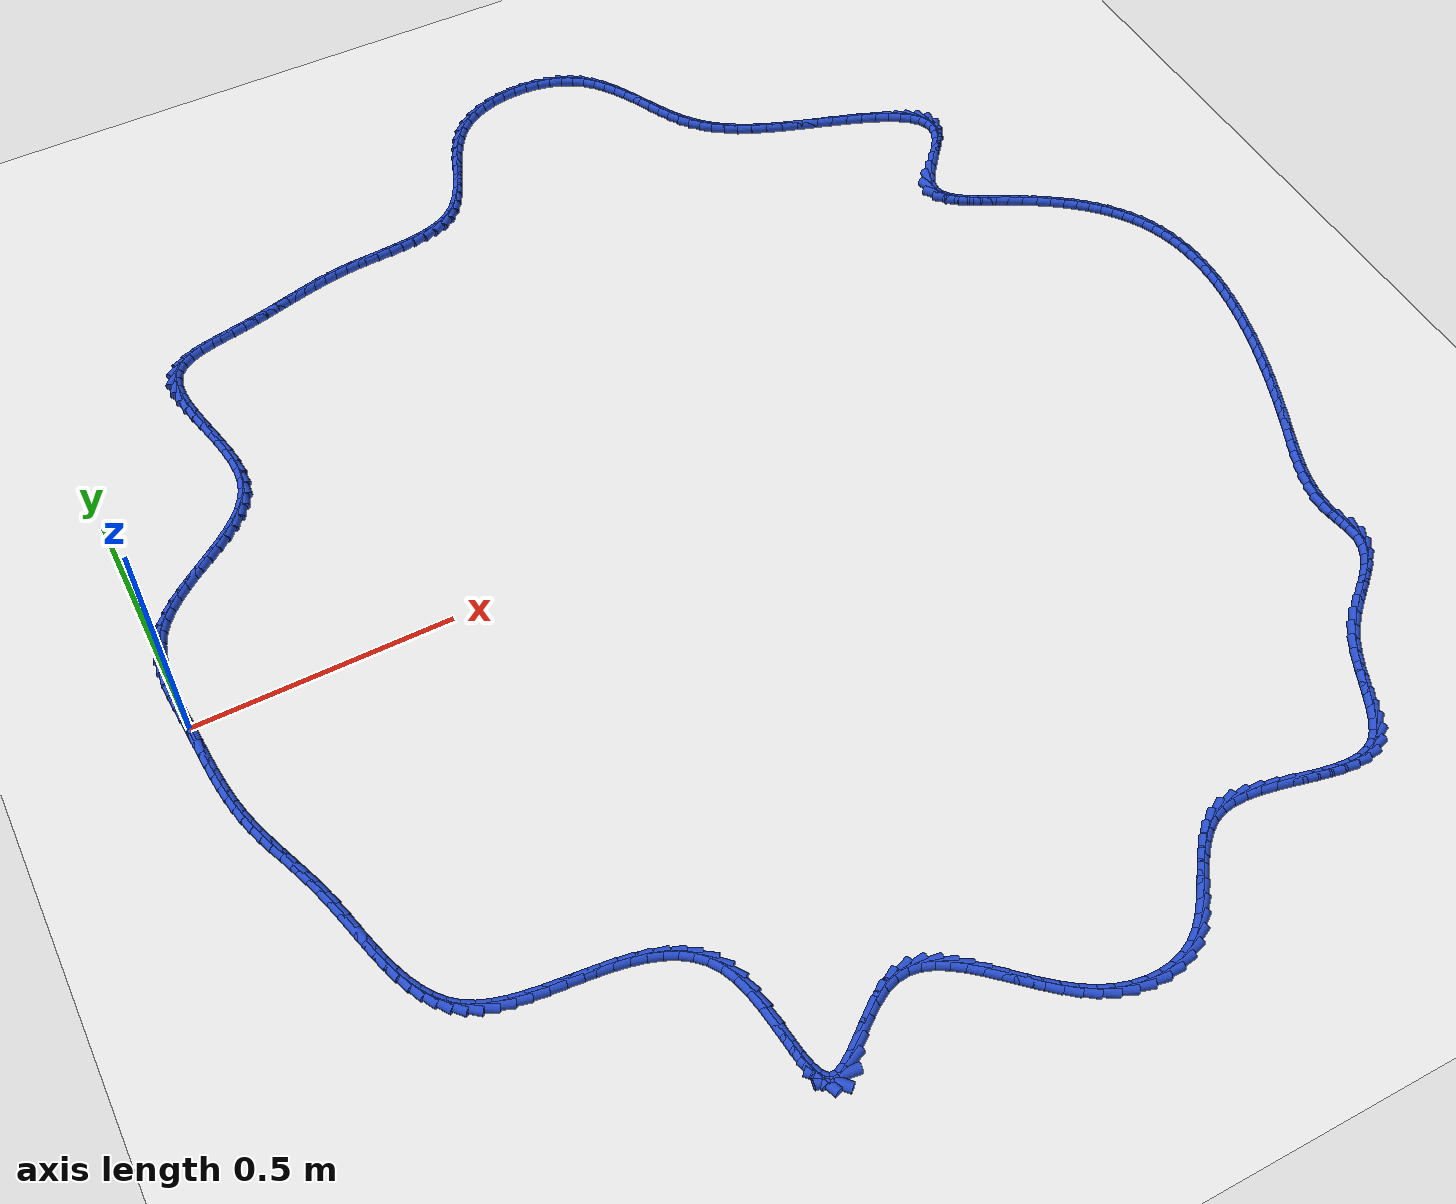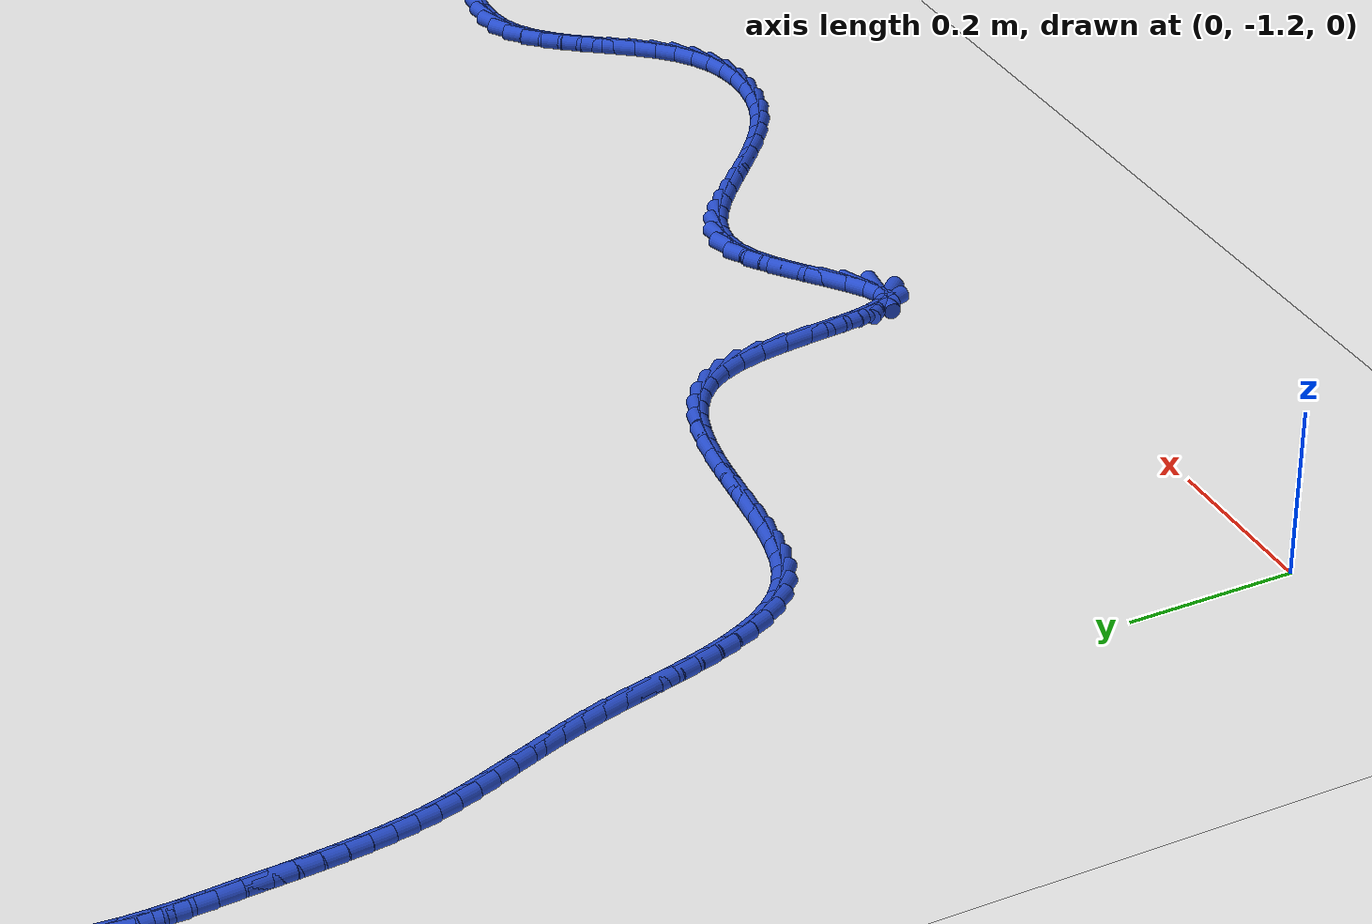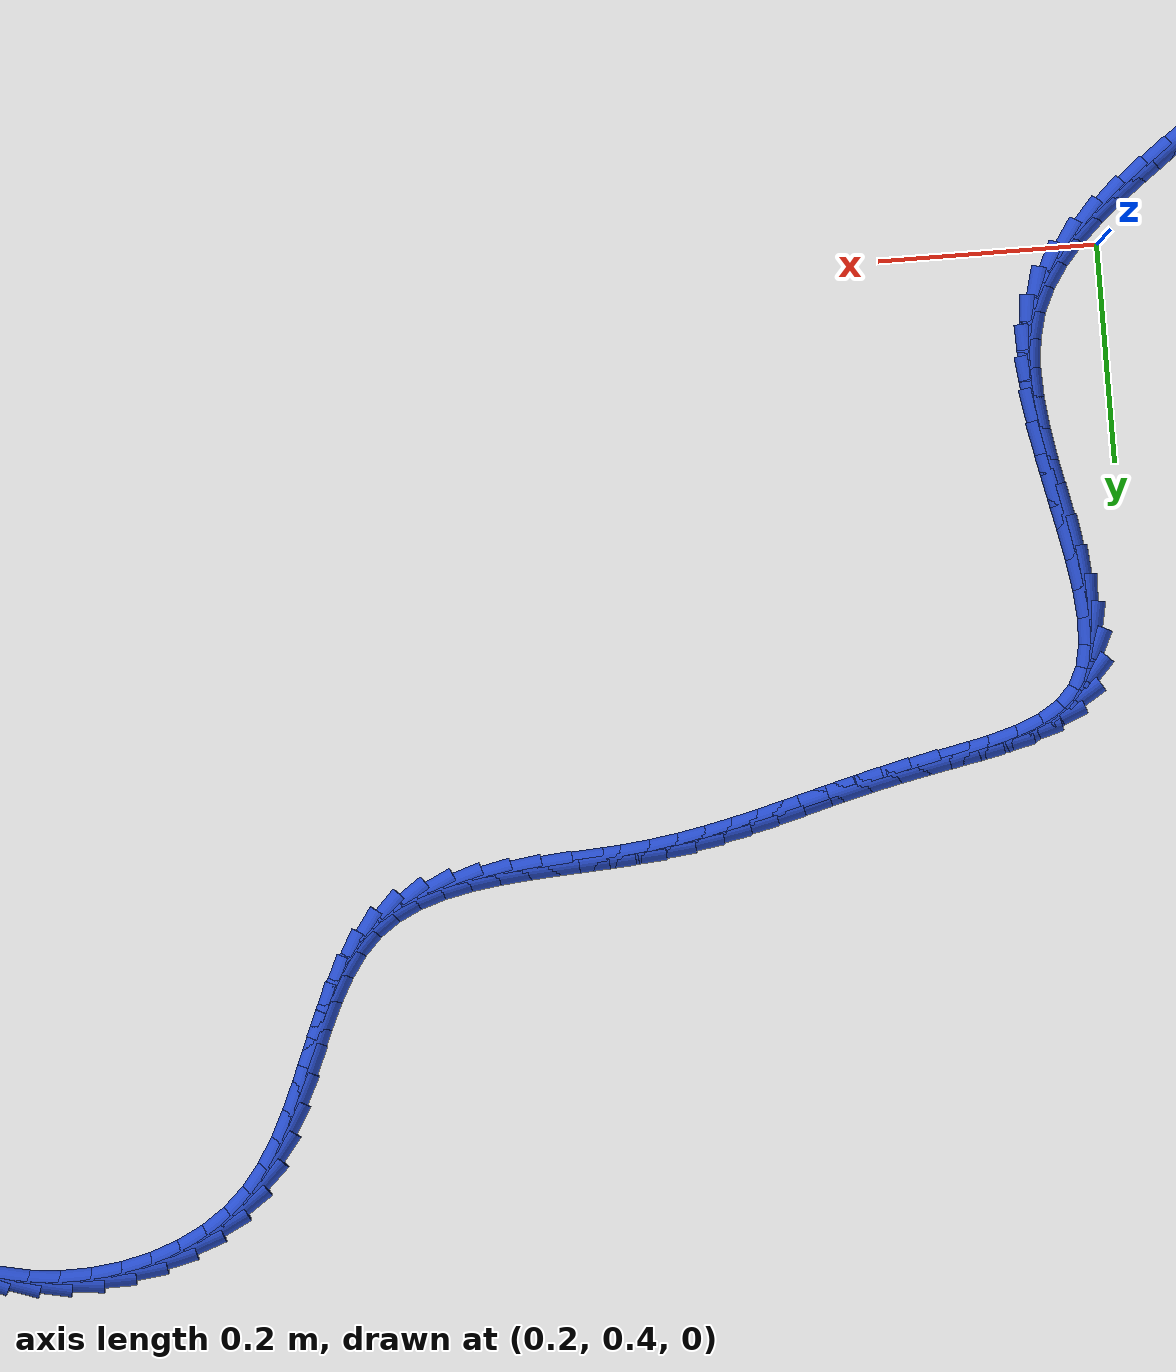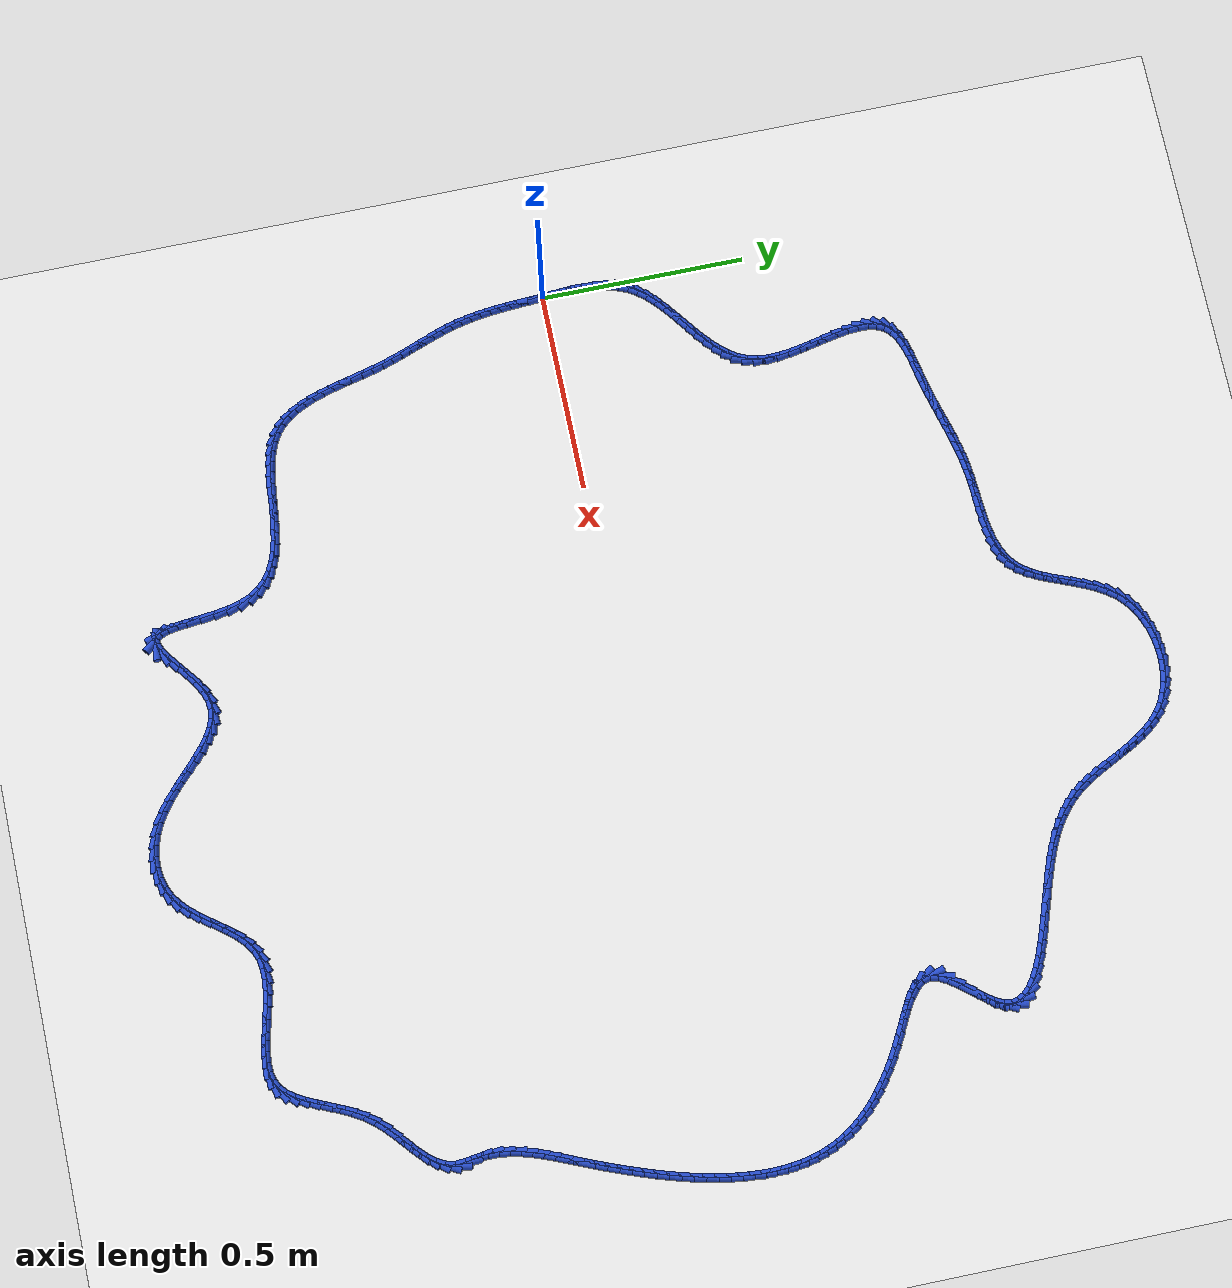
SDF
<sdf version="1.6">
 <world name="default">
  <light name="sun" type="directional">
   <pose>0 0 10 0 -0 0</pose>
   <diffuse>0.8 0.8 0.8 1</diffuse>
   <specular>0.2 0.2 0.2 1</specular>
   <attenuation>
    <range>1000</range>
    <constant>0.9</constant>
    <linear>0.01</linear>
    <quadratic>0.001</quadratic>
   </attenuation>
   <direction>-0.5 0.1 -0.9</direction>
  </light>
  <model name="ground_plane">
   <static>1</static>
   <link name="link">
    <collision name="collision">
     <geometry><plane><normal>0 0 1</normal><size>100 100</size></plane></geometry>
     <surface><friction><ode><mu>100</mu><mu2>50</mu2></ode></friction></surface>
    </collision>
    <visual name="visual">
     <cast_shadows>0</cast_shadows>
     <geometry><plane><normal>0 0 1</normal><size>100 100</size></plane></geometry>
     <material>
      <script><uri>file://media/materials/scripts/gazebo.material</uri><name>Gazebo/WhiteGlow</name></script>
     </material>
    </visual>
   </link>
  </model>
  <gravity>0 0 -9.8</gravity>
  <magnetic_field>6e-06 2.3e-05 -4.2e-05</magnetic_field>
  <atmosphere type="adiabatic"/>
  <physics name="default_physics" default="0" type="ode">
   <max_step_size>0.001</max_step_size>
   <real_time_factor>1</real_time_factor>
   <real_time_update_rate>1000</real_time_update_rate>
  </physics>
  <scene><ambient>0.4 0.4 0.4 1</ambient><background>0.7 0.7 0.7 1</background><shadows>1</shadows></scene>
  <spherical_coordinates>
   <surface_model>EARTH_WGS84</surface_model>
   <latitude_deg>0</latitude_deg>
   <longitude_deg>0</longitude_deg>
   <elevation>0</elevation>
   <heading_deg>0</heading_deg>
  </spherical_coordinates>
  <model name="line">
   <link name="link_0">
    <pose>3.0357660829594124e-18 1.457167719820518e-16 0.01 0 1.57 -1.5142388703939624</pose>
    <collision name="collision">
     <geometry><cylinder><radius>0.01</radius><length>0.08</length></cylinder></geometry>
    </collision>
    <visual name="visual">
     <material>
      <script><name>Gazebo/Blue</name><uri>file://media/materials/scripts/gazebo.material</uri></script>
     </material>
     <geometry><cylinder><radius>0.01</radius><length>0.08</length></cylinder></geometry>
    </visual>
   </link>
   <link name="link_1">
    <pose>-0.001573101638511119 0.027784558628592738 0.01 0 1.57 -1.524897964280129</pose>
    <collision name="collision">
     <geometry><cylinder><radius>0.01</radius><length>0.08</length></cylinder></geometry>
    </collision>
    <visual name="visual">
     <material>
      <script><name>Gazebo/Blue</name><uri>file://media/materials/scripts/gazebo.material</uri></script>
     </material>
     <geometry><cylinder><radius>0.01</radius><length>0.08</length></cylinder></geometry>
    </visual>
   </link>
   <link name="link_2">
    <pose>-0.0028533487512401143 0.055658057841972974 0.01 0 1.57 -1.5515178897495352</pose>
    <collision name="collision">
     <geometry><cylinder><radius>0.01</radius><length>0.08</length></cylinder></geometry>
    </collision>
    <visual name="visual">
     <material>
      <script><name>Gazebo/Blue</name><uri>file://media/materials/scripts/gazebo.material</uri></script>
     </material>
     <geometry><cylinder><radius>0.01</radius><length>0.08</length></cylinder></geometry>
    </visual>
   </link>
   <link name="link_3">
    <pose>-0.003387599189018616 0.08336695606374567 0.01 0 1.57 1.5464380096162942</pose>
    <collision name="collision">
     <geometry><cylinder><radius>0.01</radius><length>0.08</length></cylinder></geometry>
    </collision>
    <visual name="visual">
     <material>
      <script><name>Gazebo/Blue</name><uri>file://media/materials/scripts/gazebo.material</uri></script>
     </material>
     <geometry><cylinder><radius>0.01</radius><length>0.08</length></cylinder></geometry>
    </visual>
   </link>
   <link name="link_4">
    <pose>-0.0027227108026782543 0.1106577117175157 0.01 0 1.57 1.4839659882193301</pose>
    <collision name="collision">
     <geometry><cylinder><radius>0.01</radius><length>0.08</length></cylinder></geometry>
    </collision>
    <visual name="visual">
     <material>
      <script><name>Gazebo/Blue</name><uri>file://media/materials/scripts/gazebo.material</uri></script>
     </material>
     <geometry><cylinder><radius>0.01</radius><length>0.08</length></cylinder></geometry>
    </visual>
   </link>
   <link name="link_5">
    <pose>-0.00040554144305065577 0.13727678322688783 0.01 0 1.57 1.400340100375214</pose>
    <collision name="collision">
     <geometry><cylinder><radius>0.01</radius><length>0.08</length></cylinder></geometry>
    </collision>
    <visual name="visual">
     <material>
      <script><name>Gazebo/Blue</name><uri>file://media/materials/scripts/gazebo.material</uri></script>
     </material>
     <geometry><cylinder><radius>0.01</radius><length>0.08</length></cylinder></geometry>
    </visual>
   </link>
   <link name="link_6">
    <pose>0.00401705103903255 0.16297062901546686 0.01 0 1.57 1.2933699475771159</pose>
    <collision name="collision">
     <geometry><cylinder><radius>0.01</radius><length>0.08</length></cylinder></geometry>
    </collision>
    <visual name="visual">
     <material>
      <script><name>Gazebo/Blue</name><uri>file://media/materials/scripts/gazebo.material</uri></script>
     </material>
     <geometry><cylinder><radius>0.01</radius><length>0.08</length></cylinder></geometry>
    </visual>
   </link>
   <link name="link_7">
    <pose>0.010998208792739737 0.1874857075068576 0.01 0 1.57 1.1622411889832707</pose>
    <collision name="collision">
     <geometry><cylinder><radius>0.01</radius><length>0.08</length></cylinder></geometry>
    </collision>
    <visual name="visual">
     <material>
      <script><name>Gazebo/Blue</name><uri>file://media/materials/scripts/gazebo.material</uri></script>
     </material>
     <geometry><cylinder><radius>0.01</radius><length>0.08</length></cylinder></geometry>
    </visual>
   </link>
   <link name="link_8">
    <pose>0.020991073967239274 0.21056847712466498 0.01 0 1.57 1.013370379714491</pose>
    <collision name="collision">
     <geometry><cylinder><radius>0.01</radius><length>0.08</length></cylinder></geometry>
    </collision>
    <visual name="visual">
     <material>
      <script><name>Gazebo/Blue</name><uri>file://media/materials/scripts/gazebo.material</uri></script>
     </material>
     <geometry><cylinder><radius>0.01</radius><length>0.08</length></cylinder></geometry>
    </visual>
   </link>
   <link name="link_9">
    <pose>0.03435846541911029 0.23201224664798528 0.01 0 1.57 0.8814153671516375</pose>
    <collision name="collision">
     <geometry><cylinder><radius>0.01</radius><length>0.08</length></cylinder></geometry>
    </collision>
    <visual name="visual">
     <material>
      <script><name>Gazebo/Blue</name><uri>file://media/materials/scripts/gazebo.material</uri></script>
     </material>
     <geometry><cylinder><radius>0.01</radius><length>0.08</length></cylinder></geometry>
    </visual>
   </link>
   <link name="link_10">
    <pose>0.05079764593346319 0.2519555463115774 0.01 0 1.57 0.7807491866684296</pose>
    <collision name="collision">
     <geometry><cylinder><radius>0.01</radius><length>0.08</length></cylinder></geometry>
    </collision>
    <visual name="visual">
     <material>
      <script><name>Gazebo/Blue</name><uri>file://media/materials/scripts/gazebo.material</uri></script>
     </material>
     <geometry><cylinder><radius>0.01</radius><length>0.08</length></cylinder></geometry>
    </visual>
   </link>
   <link name="link_11">
    <pose>0.06970835082238525 0.27069123274243007 0.01 0 1.57 0.7088960014780832</pose>
    <collision name="collision">
     <geometry><cylinder><radius>0.01</radius><length>0.08</length></cylinder></geometry>
    </collision>
    <visual name="visual">
     <material>
      <script><name>Gazebo/Blue</name><uri>file://media/materials/scripts/gazebo.material</uri></script>
     </material>
     <geometry><cylinder><radius>0.01</radius><length>0.08</length></cylinder></geometry>
    </visual>
   </link>
   <link name="link_12">
    <pose>0.09048892853185583 0.2885128819298177 0.01 0 1.57 0.6625143995143489</pose>
    <collision name="collision">
     <geometry><cylinder><radius>0.01</radius><length>0.08</length></cylinder></geometry>
    </collision>
    <visual name="visual">
     <material>
      <script><name>Gazebo/Blue</name><uri>file://media/materials/scripts/gazebo.material</uri></script>
     </material>
     <geometry><cylinder><radius>0.01</radius><length>0.08</length></cylinder></geometry>
    </visual>
   </link>
   <link name="link_13">
    <pose>0.11253772750785415 0.30571406986301447 0.01 0 1.57 0.6389148015976219</pose>
    <collision name="collision">
     <geometry><cylinder><radius>0.01</radius><length>0.08</length></cylinder></geometry>
    </collision>
    <visual name="visual">
     <material>
      <script><name>Gazebo/Blue</name><uri>file://media/materials/scripts/gazebo.material</uri></script>
     </material>
     <geometry><cylinder><radius>0.01</radius><length>0.08</length></cylinder></geometry>
    </visual>
   </link>
   <link name="link_14">
    <pose>0.13525309619635947 0.32258837253129463 0.01 0 1.57 0.6366044481341545</pose>
    <collision name="collision">
     <geometry><cylinder><radius>0.01</radius><length>0.08</length></cylinder></geometry>
    </collision>
    <visual name="visual">
     <material>
      <script><name>Gazebo/Blue</name><uri>file://media/materials/scripts/gazebo.material</uri></script>
     </material>
     <geometry><cylinder><radius>0.01</radius><length>0.08</length></cylinder></geometry>
    </visual>
   </link>
   <link name="link_15">
    <pose>0.1580333830433512 0.3394293659239326 0.01 0 1.57 0.6554366983390438</pose>
    <collision name="collision">
     <geometry><cylinder><radius>0.01</radius><length>0.08</length></cylinder></geometry>
    </collision>
    <visual name="visual">
     <material>
      <script><name>Gazebo/Blue</name><uri>file://media/materials/scripts/gazebo.material</uri></script>
     </material>
     <geometry><cylinder><radius>0.01</radius><length>0.08</length></cylinder></geometry>
    </visual>
   </link>
   <link name="link_16">
    <pose>0.18027693649480855 0.35653062603020247 0.01 0 1.57 0.6966217642238259</pose>
    <collision name="collision">
     <geometry><cylinder><radius>0.01</radius><length>0.08</length></cylinder></geometry>
    </collision>
    <visual name="visual">
     <material>
      <script><name>Gazebo/Blue</name><uri>file://media/materials/scripts/gazebo.material</uri></script>
     </material>
     <geometry><cylinder><radius>0.01</radius><length>0.08</length></cylinder></geometry>
    </visual>
   </link>
   <link name="link_17">
    <pose>0.20138210499671072 0.3741857288393785 0.01 0 1.57 0.7626224892338953</pose>
    <collision name="collision">
     <geometry><cylinder><radius>0.01</radius><length>0.08</length></cylinder></geometry>
    </collision>
    <visual name="visual">
     <material>
      <script><name>Gazebo/Blue</name><uri>file://media/materials/scripts/gazebo.material</uri></script>
     </material>
     <geometry><cylinder><radius>0.01</radius><length>0.08</length></cylinder></geometry>
    </visual>
   </link>
   <link name="link_18">
    <pose>0.2207472369950372 0.39268825034073507 0.01 0 1.57 0.8567328615599363</pose>
    <collision name="collision">
     <geometry><cylinder><radius>0.01</radius><length>0.08</length></cylinder></geometry>
    </collision>
    <visual name="visual">
     <material>
      <script><name>Gazebo/Blue</name><uri>file://media/materials/scripts/gazebo.material</uri></script>
     </material>
     <geometry><cylinder><radius>0.01</radius><length>0.08</length></cylinder></geometry>
    </visual>
   </link>
   <link name="link_19">
    <pose>0.23777068093576703 0.41233176652354636 0.01 0 1.57 0.981873106746065</pose>
    <collision name="collision">
     <geometry><cylinder><radius>0.01</radius><length>0.08</length></cylinder></geometry>
    </collision>
    <visual name="visual">
     <material>
      <script><name>Gazebo/Blue</name><uri>file://media/materials/scripts/gazebo.material</uri></script>
     </material>
     <geometry><cylinder><radius>0.01</radius><length>0.08</length></cylinder></geometry>
    </visual>
   </link>
   <link name="link_20">
    <pose>0.25185078526487975 0.4334098533770867 0.01 0 1.57 1.1380575176344592</pose>
    <collision name="collision">
     <geometry><cylinder><radius>0.01</radius><length>0.08</length></cylinder></geometry>
    </collision>
    <visual name="visual">
     <material>
      <script><name>Gazebo/Blue</name><uri>file://media/materials/scripts/gazebo.material</uri></script>
     </material>
     <geometry><cylinder><radius>0.01</radius><length>0.08</length></cylinder></geometry>
    </visual>
   </link>
   <link name="link_21">
    <pose>0.26238589842835447 0.45621608689063037 0.01 0 1.57 1.3179124413987222</pose>
    <collision name="collision">
     <geometry><cylinder><radius>0.01</radius><length>0.08</length></cylinder></geometry>
    </collision>
    <visual name="visual">
     <material>
      <script><name>Gazebo/Blue</name><uri>file://media/materials/scripts/gazebo.material</uri></script>
     </material>
     <geometry><cylinder><radius>0.01</radius><length>0.08</length></cylinder></geometry>
    </visual>
   </link>
   <link name="link_22">
    <pose>0.26879850521428084 0.48103112983029284 0.01 0 1.57 1.4831832091265764</pose>
    <collision name="collision">
     <geometry><cylinder><radius>0.01</radius><length>0.08</length></cylinder></geometry>
    </collision>
    <visual name="visual">
     <material>
      <script><name>Gazebo/Blue</name><uri>file://media/materials/scripts/gazebo.material</uri></script>
     </material>
     <geometry><cylinder><radius>0.01</radius><length>0.08</length></cylinder></geometry>
    </visual>
   </link>
   <link name="link_23">
    <pose>0.27114931805559567 0.5077941857648482 0.01 0 1.57 -1.536789636377989</pose>
    <collision name="collision">
     <geometry><cylinder><radius>0.01</radius><length>0.08</length></cylinder></geometry>
    </collision>
    <visual name="visual">
     <material>
      <script><name>Gazebo/Blue</name><uri>file://media/materials/scripts/gazebo.material</uri></script>
     </material>
     <geometry><cylinder><radius>0.01</radius><length>0.08</length></cylinder></geometry>
    </visual>
   </link>
   <link name="link_24">
    <pose>0.27018716575591106 0.5360763080183952 0.01 0 1.57 -1.4523858012774253</pose>
    <collision name="collision">
     <geometry><cylinder><radius>0.01</radius><length>0.08</length></cylinder></geometry>
    </collision>
    <visual name="visual">
     <material>
      <script><name>Gazebo/Blue</name><uri>file://media/materials/scripts/gazebo.material</uri></script>
     </material>
     <geometry><cylinder><radius>0.01</radius><length>0.08</length></cylinder></geometry>
    </visual>
   </link>
   <link name="link_25">
    <pose>0.2666950089270692 0.5654302890014906 0.01 0 1.57 -1.3977791686058982</pose>
    <collision name="collision">
     <geometry><cylinder><radius>0.01</radius><length>0.08</length></cylinder></geometry>
    </collision>
    <visual name="visual">
     <material>
      <script><name>Gazebo/Blue</name><uri>file://media/materials/scripts/gazebo.material</uri></script>
     </material>
     <geometry><cylinder><radius>0.01</radius><length>0.08</length></cylinder></geometry>
    </visual>
   </link>
   <link name="link_26">
    <pose>0.2614558081809126 0.5954089211246922 0.01 0 1.57 -1.367920349699551</pose>
    <collision name="collision">
     <geometry><cylinder><radius>0.01</radius><length>0.08</length></cylinder></geometry>
    </collision>
    <visual name="visual">
     <material>
      <script><name>Gazebo/Blue</name><uri>file://media/materials/scripts/gazebo.material</uri></script>
     </material>
     <geometry><cylinder><radius>0.01</radius><length>0.08</length></cylinder></geometry>
    </visual>
   </link>
   <link name="link_27">
    <pose>0.25525252412928334 0.6255649967985576 0.01 0 1.57 -1.3603365968070227</pose>
    <collision name="collision">
     <geometry><cylinder><radius>0.01</radius><length>0.08</length></cylinder></geometry>
    </collision>
    <visual name="visual">
     <material>
      <script><name>Gazebo/Blue</name><uri>file://media/materials/scripts/gazebo.material</uri></script>
     </material>
     <geometry><cylinder><radius>0.01</radius><length>0.08</length></cylinder></geometry>
    </visual>
   </link>
   <link name="link_28">
    <pose>0.24886811738402376 0.655451308433644 0.01 0 1.57 -1.3750923640152828</pose>
    <collision name="collision">
     <geometry><cylinder><radius>0.01</radius><length>0.08</length></cylinder></geometry>
    </collision>
    <visual name="visual">
     <material>
      <script><name>Gazebo/Blue</name><uri>file://media/materials/scripts/gazebo.material</uri></script>
     </material>
     <geometry><cylinder><radius>0.01</radius><length>0.08</length></cylinder></geometry>
    </visual>
   </link>
   <link name="link_29">
    <pose>0.24308554855697612 0.6846206484405092 0.01 0 1.57 -1.4150340864654647</pose>
    <collision name="collision">
     <geometry><cylinder><radius>0.01</radius><length>0.08</length></cylinder></geometry>
    </collision>
    <visual name="visual">
     <material>
      <script><name>Gazebo/Blue</name><uri>file://media/materials/scripts/gazebo.material</uri></script>
     </material>
     <geometry><cylinder><radius>0.01</radius><length>0.08</length></cylinder></geometry>
    </visual>
   </link>
   <link name="link_30">
    <pose>0.23868777825998266 0.7126258092297102 0.01 0 1.57 -1.4865064708855675</pose>
    <collision name="collision">
     <geometry><cylinder><radius>0.01</radius><length>0.08</length></cylinder></geometry>
    </collision>
    <visual name="visual">
     <material>
      <script><name>Gazebo/Blue</name><uri>file://media/materials/scripts/gazebo.material</uri></script>
     </material>
     <geometry><cylinder><radius>0.01</radius><length>0.08</length></cylinder></geometry>
    </visual>
   </link>
   <link name="link_31">
    <pose>0.23645776710488567 0.7390195832118045 0.01 0 1.57 1.5411890664423105</pose>
    <collision name="collision">
     <geometry><cylinder><radius>0.01</radius><length>0.08</length></cylinder></geometry>
    </collision>
    <visual name="visual">
     <material>
      <script><name>Gazebo/Blue</name><uri>file://media/materials/scripts/gazebo.material</uri></script>
     </material>
     <geometry><cylinder><radius>0.01</radius><length>0.08</length></cylinder></geometry>
    </visual>
   </link>
   <link name="link_32">
    <pose>0.2371784757035274 0.7633547627973498 0.01 0 1.57 1.3695049922280698</pose>
    <collision name="collision">
     <geometry><cylinder><radius>0.01</radius><length>0.08</length></cylinder></geometry>
    </collision>
    <visual name="visual">
     <material>
      <script><name>Gazebo/Blue</name><uri>file://media/materials/scripts/gazebo.material</uri></script>
     </material>
     <geometry><cylinder><radius>0.01</radius><length>0.08</length></cylinder></geometry>
    </visual>
   </link>
   <link name="link_33">
    <pose>0.2416328646677502 0.7851841403969037 0.01 0 1.57 1.1271424751690373</pose>
    <collision name="collision">
     <geometry><cylinder><radius>0.01</radius><length>0.08</length></cylinder></geometry>
    </collision>
    <visual name="visual">
     <material>
      <script><name>Gazebo/Blue</name><uri>file://media/materials/scripts/gazebo.material</uri></script>
     </material>
     <geometry><cylinder><radius>0.01</radius><length>0.08</length></cylinder></geometry>
    </visual>
   </link>
   <link name="link_34">
    <pose>0.25060389460939625 0.8040605084210231 0.01 0 1.57 0.8269858121171703</pose>
    <collision name="collision">
     <geometry><cylinder><radius>0.01</radius><length>0.08</length></cylinder></geometry>
    </collision>
    <visual name="visual">
     <material>
      <script><name>Gazebo/Blue</name><uri>file://media/materials/scripts/gazebo.material</uri></script>
     </material>
     <geometry><cylinder><radius>0.01</radius><length>0.08</length></cylinder></geometry>
    </visual>
   </link>
   <link name="link_35">
    <pose>0.26485437990328886 0.8195484588265836 0.01 0 1.57 0.5571664731152798</pose>
    <collision name="collision">
     <geometry><cylinder><radius>0.01</radius><length>0.08</length></cylinder></geometry>
    </collision>
    <visual name="visual">
     <material>
      <script><name>Gazebo/Blue</name><uri>file://media/materials/scripts/gazebo.material</uri></script>
     </material>
     <geometry><cylinder><radius>0.01</radius><length>0.08</length></cylinder></geometry>
    </visual>
   </link>
   <link name="link_36">
    <pose>0.28433763234048515 0.8316867050266186 0.01 0 1.57 0.38091957048348446</pose>
    <collision name="collision">
     <geometry><cylinder><radius>0.01</radius><length>0.08</length></cylinder></geometry>
    </collision>
    <visual name="visual">
     <material>
      <script><name>Gazebo/Blue</name><uri>file://media/materials/scripts/gazebo.material</uri></script>
     </material>
     <geometry><cylinder><radius>0.01</radius><length>0.08</length></cylinder></geometry>
    </visual>
   </link>
   <link name="link_37">
    <pose>0.3079399075796144 0.8411389296652115 0.01 0 1.57 0.27450635002502277</pose>
    <collision name="collision">
     <geometry><cylinder><radius>0.01</radius><length>0.08</length></cylinder></geometry>
    </collision>
    <visual name="visual">
     <material>
      <script><name>Gazebo/Blue</name><uri>file://media/materials/scripts/gazebo.material</uri></script>
     </material>
     <geometry><cylinder><radius>0.01</radius><length>0.08</length></cylinder></geometry>
    </visual>
   </link>
   <link name="link_38">
    <pose>0.33447456900766415 0.8486115080111091 0.01 0 1.57 0.2157952483238712</pose>
    <collision name="collision">
     <geometry><cylinder><radius>0.01</radius><length>0.08</length></cylinder></geometry>
    </collision>
    <visual name="visual">
     <material>
      <script><name>Gazebo/Blue</name><uri>file://media/materials/scripts/gazebo.material</uri></script>
     </material>
     <geometry><cylinder><radius>0.01</radius><length>0.08</length></cylinder></geometry>
    </visual>
   </link>
   <link name="link_39">
    <pose>0.36275498001162254 0.8548108153330591 0.01 0 1.57 0.19287402628280426</pose>
    <collision name="collision">
     <geometry><cylinder><radius>0.01</radius><length>0.08</length></cylinder></geometry>
    </collision>
    <visual name="visual">
     <material>
      <script><name>Gazebo/Blue</name><uri>file://media/materials/scripts/gazebo.material</uri></script>
     </material>
     <geometry><cylinder><radius>0.01</radius><length>0.08</length></cylinder></geometry>
    </visual>
   </link>
   <link name="link_40">
    <pose>0.39159450397847717 0.8604432268998085 0.01 0 1.57 0.20118924336315208</pose>
    <collision name="collision">
     <geometry><cylinder><radius>0.01</radius><length>0.08</length></cylinder></geometry>
    </collision>
    <visual name="visual">
     <material>
      <script><name>Gazebo/Blue</name><uri>file://media/materials/scripts/gazebo.material</uri></script>
     </material>
     <geometry><cylinder><radius>0.01</radius><length>0.08</length></cylinder></geometry>
    </visual>
   </link>
   <link name="link_41">
    <pose>0.4198286737873333 0.8662015419458791 0.01 0 1.57 0.22434620311010006</pose>
    <collision name="collision">
     <geometry><cylinder><radius>0.01</radius><length>0.08</length></cylinder></geometry>
    </collision>
    <visual name="visual">
     <material>
      <script><name>Gazebo/Blue</name><uri>file://media/materials/scripts/gazebo.material</uri></script>
     </material>
     <geometry><cylinder><radius>0.01</radius><length>0.08</length></cylinder></geometry>
    </visual>
   </link>
   <link name="link_42">
    <pose>0.44693329170229457 0.8723864749869115 0.01 0 1.57 0.24233790065833596</pose>
    <collision name="collision">
     <geometry><cylinder><radius>0.01</radius><length>0.08</length></cylinder></geometry>
    </collision>
    <visual name="visual">
     <material>
      <script><name>Gazebo/Blue</name><uri>file://media/materials/scripts/gazebo.material</uri></script>
     </material>
     <geometry><cylinder><radius>0.01</radius><length>0.08</length></cylinder></geometry>
    </visual>
   </link>
   <link name="link_43">
    <pose>0.47310651112427277 0.8788563910384096 0.01 0 1.57 0.2530862116136959</pose>
    <collision name="collision">
     <geometry><cylinder><radius>0.01</radius><length>0.08</length></cylinder></geometry>
    </collision>
    <visual name="visual">
     <material>
      <script><name>Gazebo/Blue</name><uri>file://media/materials/scripts/gazebo.material</uri></script>
     </material>
     <geometry><cylinder><radius>0.01</radius><length>0.08</length></cylinder></geometry>
    </visual>
   </link>
   <link name="link_44">
    <pose>0.4985851462086352 0.8854459802512066 0.01 0 1.57 0.2558098369335754</pose>
    <collision name="collision">
     <geometry><cylinder><radius>0.01</radius><length>0.08</length></cylinder></geometry>
    </collision>
    <visual name="visual">
     <material>
      <script><name>Gazebo/Blue</name><uri>file://media/materials/scripts/gazebo.material</uri></script>
     </material>
     <geometry><cylinder><radius>0.01</radius><length>0.08</length></cylinder></geometry>
    </visual>
   </link>
   <link name="link_45">
    <pose>0.523606011110749 0.8919899327761356 0.01 0 1.57 0.25002080515490976</pose>
    <collision name="collision">
     <geometry><cylinder><radius>0.01</radius><length>0.08</length></cylinder></geometry>
    </collision>
    <visual name="visual">
     <material>
      <script><name>Gazebo/Blue</name><uri>file://media/materials/scripts/gazebo.material</uri></script>
     </material>
     <geometry><cylinder><radius>0.01</radius><length>0.08</length></cylinder></geometry>
    </visual>
   </link>
   <link name="link_46">
    <pose>0.5484059199859805 0.8983229387640296 0.01 0 1.57 0.23558176893066318</pose>
    <collision name="collision">
     <geometry><cylinder><radius>0.01</radius><length>0.08</length></cylinder></geometry>
    </collision>
    <visual name="visual">
     <material>
      <script><name>Gazebo/Blue</name><uri>file://media/materials/scripts/gazebo.material</uri></script>
     </material>
     <geometry><cylinder><radius>0.01</radius><length>0.08</length></cylinder></geometry>
    </visual>
   </link>
   <link name="link_47">
    <pose>0.5732216869896974 0.9042796883657219 0.01 0 1.57 0.21274704398890315</pose>
    <collision name="collision">
     <geometry><cylinder><radius>0.01</radius><length>0.08</length></cylinder></geometry>
    </collision>
    <visual name="visual">
     <material>
      <script><name>Gazebo/Blue</name><uri>file://media/materials/scripts/gazebo.material</uri></script>
     </material>
     <geometry><cylinder><radius>0.01</radius><length>0.08</length></cylinder></geometry>
    </visual>
   </link>
   <link name="link_48">
    <pose>0.5982901262772666 0.909694871732046 0.01 0 1.57 0.18217846485780043</pose>
    <collision name="collision">
     <geometry><cylinder><radius>0.01</radius><length>0.08</length></cylinder></geometry>
    </collision>
    <visual name="visual">
     <material>
      <script><name>Gazebo/Blue</name><uri>file://media/materials/scripts/gazebo.material</uri></script>
     </material>
     <geometry><cylinder><radius>0.01</radius><length>0.08</length></cylinder></geometry>
    </visual>
   </link>
   <link name="link_49">
    <pose>0.623848052004055 0.9144031790138349 0.01 0 1.57 0.14492444308787372</pose>
    <collision name="collision">
     <geometry><cylinder><radius>0.01</radius><length>0.08</length></cylinder></geometry>
    </collision>
    <visual name="visual">
     <material>
      <script><name>Gazebo/Blue</name><uri>file://media/materials/scripts/gazebo.material</uri></script>
     </material>
     <geometry><cylinder><radius>0.01</radius><length>0.08</length></cylinder></geometry>
    </visual>
   </link>
   <link name="link_50">
    <pose>0.6501322783254295 0.9182393003619215 0.01 0 1.57 0.10310828392380683</pose>
    <collision name="collision">
     <geometry><cylinder><radius>0.01</radius><length>0.08</length></cylinder></geometry>
    </collision>
    <visual name="visual">
     <material>
      <script><name>Gazebo/Blue</name><uri>file://media/materials/scripts/gazebo.material</uri></script>
     </material>
     <geometry><cylinder><radius>0.01</radius><length>0.08</length></cylinder></geometry>
    </visual>
   </link>
   <link name="link_51">
    <pose>0.677360974737244 0.921056796171042 0.01 0 1.57 0.07105435621257762</pose>
    <collision name="collision">
     <geometry><cylinder><radius>0.01</radius><length>0.08</length></cylinder></geometry>
    </collision>
    <visual name="visual">
     <material>
      <script><name>Gazebo/Blue</name><uri>file://media/materials/scripts/gazebo.material</uri></script>
     </material>
     <geometry><cylinder><radius>0.01</radius><length>0.08</length></cylinder></geometry>
    </visual>
   </link>
   <link name="link_52">
    <pose>0.7054123233320791 0.9230533277951959 0.01 0 1.57 0.05875239474969498</pose>
    <collision name="collision">
     <geometry><cylinder><radius>0.01</radius><length>0.08</length></cylinder></geometry>
    </collision>
    <visual name="visual">
     <material>
      <script><name>Gazebo/Blue</name><uri>file://media/materials/scripts/gazebo.material</uri></script>
     </material>
     <geometry><cylinder><radius>0.01</radius><length>0.08</length></cylinder></geometry>
    </visual>
   </link>
   <link name="link_53">
    <pose>0.733867586351295 0.9247270689151497 0.01 0 1.57 0.06530260756865779</pose>
    <collision name="collision">
     <geometry><cylinder><radius>0.01</radius><length>0.08</length></cylinder></geometry>
    </collision>
    <visual name="visual">
     <material>
      <script><name>Gazebo/Blue</name><uri>file://media/materials/scripts/gazebo.material</uri></script>
     </material>
     <geometry><cylinder><radius>0.01</radius><length>0.08</length></cylinder></geometry>
    </visual>
   </link>
   <link name="link_54">
    <pose>0.7622980444536112 0.926586295562899 0.01 0 1.57 0.09100128806174924</pose>
    <collision name="collision">
     <geometry><cylinder><radius>0.01</radius><length>0.08</length></cylinder></geometry>
    </collision>
    <visual name="visual">
     <material>
      <script><name>Gazebo/Blue</name><uri>file://media/materials/scripts/gazebo.material</uri></script>
     </material>
     <geometry><cylinder><radius>0.01</radius><length>0.08</length></cylinder></geometry>
    </visual>
   </link>
   <link name="link_55">
    <pose>0.790274978297749 0.9291392837704403 0.01 0 1.57 0.13771178994860755</pose>
    <collision name="collision">
     <geometry><cylinder><radius>0.01</radius><length>0.08</length></cylinder></geometry>
    </collision>
    <visual name="visual">
     <material>
      <script><name>Gazebo/Blue</name><uri>file://media/materials/scripts/gazebo.material</uri></script>
     </material>
     <geometry><cylinder><radius>0.01</radius><length>0.08</length></cylinder></geometry>
    </visual>
   </link>
   <link name="link_56">
    <pose>0.8173696685424287 0.9328943095697688 0.01 0 1.57 0.20887685441671777</pose>
    <collision name="collision">
     <geometry><cylinder><radius>0.01</radius><length>0.08</length></cylinder></geometry>
    </collision>
    <visual name="visual">
     <material>
      <script><name>Gazebo/Blue</name><uri>file://media/materials/scripts/gazebo.material</uri></script>
     </material>
     <geometry><cylinder><radius>0.01</radius><length>0.08</length></cylinder></geometry>
    </visual>
   </link>
   <link name="link_57">
    <pose>0.8431533958463701 0.9383596489928803 0.01 0 1.57 0.30931938928117136</pose>
    <collision name="collision">
     <geometry><cylinder><radius>0.01</radius><length>0.08</length></cylinder></geometry>
    </collision>
    <visual name="visual">
     <material>
      <script><name>Gazebo/Blue</name><uri>file://media/materials/scripts/gazebo.material</uri></script>
     </material>
     <geometry><cylinder><radius>0.01</radius><length>0.08</length></cylinder></geometry>
    </visual>
   </link>
   <link name="link_58">
    <pose>0.867197440868294 0.9460435780717705 0.01 0 1.57 0.4441889619875084</pose>
    <collision name="collision">
     <geometry><cylinder><radius>0.01</radius><length>0.08</length></cylinder></geometry>
    </collision>
    <visual name="visual">
     <material>
      <script><name>Gazebo/Blue</name><uri>file://media/materials/scripts/gazebo.material</uri></script>
     </material>
     <geometry><cylinder><radius>0.01</radius><length>0.08</length></cylinder></geometry>
    </visual>
   </link>
   <link name="link_59">
    <pose>0.8890730842669203 0.9564543728384354 0.01 0 1.57 0.6159463296051844</pose>
    <collision name="collision">
     <geometry><cylinder><radius>0.01</radius><length>0.08</length></cylinder></geometry>
    </collision>
    <visual name="visual">
     <material>
      <script><name>Gazebo/Blue</name><uri>file://media/materials/scripts/gazebo.material</uri></script>
     </material>
     <geometry><cylinder><radius>0.01</radius><length>0.08</length></cylinder></geometry>
    </visual>
   </link>
   <link name="link_60">
    <pose>0.9083518604116103 0.9701000244588895 0.01 0 1.57 0.8044559085383504</pose>
    <collision name="collision">
     <geometry><cylinder><radius>0.01</radius><length>0.08</length></cylinder></geometry>
    </collision>
    <visual name="visual">
     <material>
      <script><name>Gazebo/Blue</name><uri>file://media/materials/scripts/gazebo.material</uri></script>
     </material>
     <geometry><cylinder><radius>0.01</radius><length>0.08</length></cylinder></geometry>
    </visual>
   </link>
   <link name="link_61">
    <pose>0.9248381963469678 0.9872270325025454 0.01 0 1.57 0.9572533420258721</pose>
    <collision name="collision">
     <geometry><cylinder><radius>0.01</radius><length>0.08</length></cylinder></geometry>
    </collision>
    <visual name="visual">
     <material>
      <script><name>Gazebo/Blue</name><uri>file://media/materials/scripts/gazebo.material</uri></script>
     </material>
     <geometry><cylinder><radius>0.01</radius><length>0.08</length></cylinder></geometry>
    </visual>
   </link>
   <link name="link_62">
    <pose>0.9389998368593798 1.0073371242304006 0.01 0 1.57 1.0656575729727458</pose>
    <collision name="collision">
     <geometry><cylinder><radius>0.01</radius><length>0.08</length></cylinder></geometry>
    </collision>
    <visual name="visual">
     <material>
      <script><name>Gazebo/Blue</name><uri>file://media/materials/scripts/gazebo.material</uri></script>
     </material>
     <geometry><cylinder><radius>0.01</radius><length>0.08</length></cylinder></geometry>
    </visual>
   </link>
   <link name="link_63">
    <pose>0.9514218378261524 1.0298003101612632 0.01 0 1.57 1.1348320544643955</pose>
    <collision name="collision">
     <geometry><cylinder><radius>0.01</radius><length>0.08</length></cylinder></geometry>
    </collision>
    <visual name="visual">
     <material>
      <script><name>Gazebo/Blue</name><uri>file://media/materials/scripts/gazebo.material</uri></script>
     </material>
     <geometry><cylinder><radius>0.01</radius><length>0.08</length></cylinder></geometry>
    </visual>
   </link>
   <link name="link_64">
    <pose>0.9626892551245904 1.0539866008139387 0.01 0 1.57 1.1704631951919957</pose>
    <collision name="collision">
     <geometry><cylinder><radius>0.01</radius><length>0.08</length></cylinder></geometry>
    </collision>
    <visual name="visual">
     <material>
      <script><name>Gazebo/Blue</name><uri>file://media/materials/scripts/gazebo.material</uri></script>
     </material>
     <geometry><cylinder><radius>0.01</radius><length>0.08</length></cylinder></geometry>
    </visual>
   </link>
   <link name="link_65">
    <pose>0.9733871446319992 1.0792660067072357 0.01 0 1.57 1.1764235700115273</pose>
    <collision name="collision">
     <geometry><cylinder><radius>0.01</radius><length>0.08</length></cylinder></geometry>
    </collision>
    <visual name="visual">
     <material>
      <script><name>Gazebo/Blue</name><uri>file://media/materials/scripts/gazebo.material</uri></script>
     </material>
     <geometry><cylinder><radius>0.01</radius><length>0.08</length></cylinder></geometry>
    </visual>
   </link>
   <link name="link_66">
    <pose>0.984100562225684 1.10500853835996 0.01 0 1.57 1.154302546132972</pose>
    <collision name="collision">
     <geometry><cylinder><radius>0.01</radius><length>0.08</length></cylinder></geometry>
    </collision>
    <visual name="visual">
     <material>
      <script><name>Gazebo/Blue</name><uri>file://media/materials/scripts/gazebo.material</uri></script>
     </material>
     <geometry><cylinder><radius>0.01</radius><length>0.08</length></cylinder></geometry>
    </visual>
   </link>
   <link name="link_67">
    <pose>0.9954145637829506 1.1305842062909193 0.01 0 1.57 1.103596077825522</pose>
    <collision name="collision">
     <geometry><cylinder><radius>0.01</radius><length>0.08</length></cylinder></geometry>
    </collision>
    <visual name="visual">
     <material>
      <script><name>Gazebo/Blue</name><uri>file://media/materials/scripts/gazebo.material</uri></script>
     </material>
     <geometry><cylinder><radius>0.01</radius><length>0.08</length></cylinder></geometry>
    </visual>
   </link>
   <link name="link_68">
    <pose>1.0079142051811034 1.1553630210189199 0.01 0 1.57 1.0222566667633124</pose>
    <collision name="collision">
     <geometry><cylinder><radius>0.01</radius><length>0.08</length></cylinder></geometry>
    </collision>
    <visual name="visual">
     <material>
      <script><name>Gazebo/Blue</name><uri>file://media/materials/scripts/gazebo.material</uri></script>
     </material>
     <geometry><cylinder><radius>0.01</radius><length>0.08</length></cylinder></geometry>
    </visual>
   </link>
   <link name="link_69">
    <pose>1.0221845422974485 1.1787149930627696 0.01 0 1.57 0.9079065773738728</pose>
    <collision name="collision">
     <geometry><cylinder><radius>0.01</radius><length>0.08</length></cylinder></geometry>
    </collision>
    <visual name="visual">
     <material>
      <script><name>Gazebo/Blue</name><uri>file://media/materials/scripts/gazebo.material</uri></script>
     </material>
     <geometry><cylinder><radius>0.01</radius><length>0.08</length></cylinder></geometry>
    </visual>
   </link>
   <link name="link_70">
    <pose>1.0388106310092906 1.2000101329412747 0.01 0 1.57 0.7610379380244364</pose>
    <collision name="collision">
     <geometry><cylinder><radius>0.01</radius><length>0.08</length></cylinder></geometry>
    </collision>
    <visual name="visual">
     <material>
      <script><name>Gazebo/Blue</name><uri>file://media/materials/scripts/gazebo.material</uri></script>
     </material>
     <geometry><cylinder><radius>0.01</radius><length>0.08</length></cylinder></geometry>
    </visual>
   </link>
   <link name="link_71">
    <pose>1.0583589213258864 1.2186284911439786 0.01 0 1.57 0.6060542507324087</pose>
    <collision name="collision">
     <geometry><cylinder><radius>0.01</radius><length>0.08</length></cylinder></geometry>
    </collision>
    <visual name="visual">
     <material>
      <script><name>Gazebo/Blue</name><uri>file://media/materials/scripts/gazebo.material</uri></script>
     </material>
     <geometry><cylinder><radius>0.01</radius><length>0.08</length></cylinder></geometry>
    </visual>
   </link>
   <link name="link_72">
    <pose>1.0808731000513179 1.234232208050986 0.01 0 1.57 0.4666572311444285</pose>
    <collision name="collision">
     <geometry><cylinder><radius>0.01</radius><length>0.08</length></cylinder></geometry>
    </collision>
    <visual name="visual">
     <material>
      <script><name>Gazebo/Blue</name><uri>file://media/materials/scripts/gazebo.material</uri></script>
     </material>
     <geometry><cylinder><radius>0.01</radius><length>0.08</length></cylinder></geometry>
    </visual>
   </link>
   <link name="link_73">
    <pose>1.1058152571030393 1.2467972613600926 0.01 0 1.57 0.34125926283778646</pose>
    <collision name="collision">
     <geometry><cylinder><radius>0.01</radius><length>0.08</length></cylinder></geometry>
    </collision>
    <visual name="visual">
     <material>
      <script><name>Gazebo/Blue</name><uri>file://media/materials/scripts/gazebo.material</uri></script>
     </material>
     <geometry><cylinder><radius>0.01</radius><length>0.08</length></cylinder></geometry>
    </visual>
   </link>
   <link name="link_74">
    <pose>1.1326170678237697 1.2563160408730336 0.01 0 1.57 0.22618581099302873</pose>
    <collision name="collision">
     <geometry><cylinder><radius>0.01</radius><length>0.08</length></cylinder></geometry>
    </collision>
    <visual name="visual">
     <material>
      <script><name>Gazebo/Blue</name><uri>file://media/materials/scripts/gazebo.material</uri></script>
     </material>
     <geometry><cylinder><radius>0.01</radius><length>0.08</length></cylinder></geometry>
    </visual>
   </link>
   <link name="link_75">
    <pose>1.1607102075562288 1.2627809363915448 0.01 0 1.57 0.11756282723773595</pose>
    <collision name="collision">
     <geometry><cylinder><radius>0.01</radius><length>0.08</length></cylinder></geometry>
    </collision>
    <visual name="visual">
     <material>
      <script><name>Gazebo/Blue</name><uri>file://media/materials/scripts/gazebo.material</uri></script>
     </material>
     <geometry><cylinder><radius>0.01</radius><length>0.08</length></cylinder></geometry>
    </visual>
   </link>
   <link name="link_76">
    <pose>1.1895263516431351 1.2661843377173596 0.01 0 1.57 0.011538577613577133</pose>
    <collision name="collision">
     <geometry><cylinder><radius>0.01</radius><length>0.08</length></cylinder></geometry>
    </collision>
    <visual name="visual">
     <material>
      <script><name>Gazebo/Blue</name><uri>file://media/materials/scripts/gazebo.material</uri></script>
     </material>
     <geometry><cylinder><radius>0.01</radius><length>0.08</length></cylinder></geometry>
    </visual>
   </link>
   <link name="link_77">
    <pose>1.2184971754272085 1.2665186346522144 0.01 0 1.57 -0.09573892435135192</pose>
    <collision name="collision">
     <geometry><cylinder><radius>0.01</radius><length>0.08</length></cylinder></geometry>
    </collision>
    <visual name="visual">
     <material>
      <script><name>Gazebo/Blue</name><uri>file://media/materials/scripts/gazebo.material</uri></script>
     </material>
     <geometry><cylinder><radius>0.01</radius><length>0.08</length></cylinder></geometry>
    </visual>
   </link>
   <link name="link_78">
    <pose>1.2470543542511672 1.2637762169978428 0.01 0 1.57 -0.20824045659383092</pose>
    <collision name="collision">
     <geometry><cylinder><radius>0.01</radius><length>0.08</length></cylinder></geometry>
    </collision>
    <visual name="visual">
     <material>
      <script><name>Gazebo/Blue</name><uri>file://media/materials/scripts/gazebo.material</uri></script>
     </material>
     <geometry><cylinder><radius>0.01</radius><length>0.08</length></cylinder></geometry>
    </visual>
   </link>
   <link name="link_79">
    <pose>1.2746295634577316 1.257949474555981 0.01 0 1.57 -0.3301546396664207</pose>
    <collision name="collision">
     <geometry><cylinder><radius>0.01</radius><length>0.08</length></cylinder></geometry>
    </collision>
    <visual name="visual">
     <material>
      <script><name>Gazebo/Blue</name><uri>file://media/materials/scripts/gazebo.material</uri></script>
     </material>
     <geometry><cylinder><radius>0.01</radius><length>0.08</length></cylinder></geometry>
    </visual>
   </link>
   <link name="link_80">
    <pose>1.3006544783896192 1.2490307971283632 0.01 0 1.57 -0.46582289307321006</pose>
    <collision name="collision">
     <geometry><cylinder><radius>0.01</radius><length>0.08</length></cylinder></geometry>
    </collision>
    <visual name="visual">
     <material>
      <script><name>Gazebo/Blue</name><uri>file://media/materials/scripts/gazebo.material</uri></script>
     </material>
     <geometry><cylinder><radius>0.01</radius><length>0.08</length></cylinder></geometry>
    </visual>
   </link>
   <link name="link_81">
    <pose>1.3245607743895507 1.2370125745167244 0.01 0 1.57 -0.616027699357937</pose>
    <collision name="collision">
     <geometry><cylinder><radius>0.01</radius><length>0.08</length></cylinder></geometry>
    </collision>
    <visual name="visual">
     <material>
      <script><name>Gazebo/Blue</name><uri>file://media/materials/scripts/gazebo.material</uri></script>
     </material>
     <geometry><cylinder><radius>0.01</radius><length>0.08</length></cylinder></geometry>
    </visual>
   </link>
   <link name="link_82">
    <pose>1.3458663190535174 1.2219297597574503 0.01 0 1.57 -0.7573669783366597</pose>
    <collision name="collision">
     <geometry><cylinder><radius>0.01</radius><length>0.08</length></cylinder></geometry>
    </collision>
    <visual name="visual">
     <material>
      <script><name>Gazebo/Blue</name><uri>file://media/materials/scripts/gazebo.material</uri></script>
     </material>
     <geometry><cylinder><radius>0.01</radius><length>0.08</length></cylinder></geometry>
    </visual>
   </link>
   <link name="link_83">
    <pose>1.3647030384406693 1.204120538642352 0.01 0 1.57 -0.8747426592702926</pose>
    <collision name="collision">
     <geometry><cylinder><radius>0.01</radius><length>0.08</length></cylinder></geometry>
    </collision>
    <visual name="visual">
     <material>
      <script><name>Gazebo/Blue</name><uri>file://media/materials/scripts/gazebo.material</uri></script>
     </material>
     <geometry><cylinder><radius>0.01</radius><length>0.08</length></cylinder></geometry>
    </visual>
   </link>
   <link name="link_84">
    <pose>1.3814693484277358 1.1840546942728223 0.01 0 1.57 -0.9662737038451166</pose>
    <collision name="collision">
     <geometry><cylinder><radius>0.01</radius><length>0.08</length></cylinder></geometry>
    </collision>
    <visual name="visual">
     <material>
      <script><name>Gazebo/Blue</name><uri>file://media/materials/scripts/gazebo.material</uri></script>
     </material>
     <geometry><cylinder><radius>0.01</radius><length>0.08</length></cylinder></geometry>
    </visual>
   </link>
   <link name="link_85">
    <pose>1.3965647457173853 1.162202543480914 0.01 0 1.57 -1.032821092238021</pose>
    <collision name="collision">
     <geometry><cylinder><radius>0.01</radius><length>0.08</length></cylinder></geometry>
    </collision>
    <visual name="visual">
     <material>
      <script><name>Gazebo/Blue</name><uri>file://media/materials/scripts/gazebo.material</uri></script>
     </material>
     <geometry><cylinder><radius>0.01</radius><length>0.08</length></cylinder></geometry>
    </visual>
   </link>
   <link name="link_86">
    <pose>1.4103887270122863 1.1390344030986774 0.01 0 1.57 -1.0761596167393974</pose>
    <collision name="collision">
     <geometry><cylinder><radius>0.01</radius><length>0.08</length></cylinder></geometry>
    </collision>
    <visual name="visual">
     <material>
      <script><name>Gazebo/Blue</name><uri>file://media/materials/scripts/gazebo.material</uri></script>
     </material>
     <geometry><cylinder><radius>0.01</radius><length>0.08</length></cylinder></geometry>
    </visual>
   </link>
   <link name="link_87">
    <pose>1.4233407890151069 1.115020589958164 0.01 0 1.57 -1.0978422841866116</pose>
    <collision name="collision">
     <geometry><cylinder><radius>0.01</radius><length>0.08</length></cylinder></geometry>
    </collision>
    <visual name="visual">
     <material>
      <script><name>Gazebo/Blue</name><uri>file://media/materials/scripts/gazebo.material</uri></script>
     </material>
     <geometry><cylinder><radius>0.01</radius><length>0.08</length></cylinder></geometry>
    </visual>
   </link>
   <link name="link_88">
    <pose>1.4358204284285143 1.0906314208914256 0.01 0 1.57 -1.0986364586509787</pose>
    <collision name="collision">
     <geometry><cylinder><radius>0.01</radius><length>0.08</length></cylinder></geometry>
    </collision>
    <visual name="visual">
     <material>
      <script><name>Gazebo/Blue</name><uri>file://media/materials/scripts/gazebo.material</uri></script>
     </material>
     <geometry><cylinder><radius>0.01</radius><length>0.08</length></cylinder></geometry>
    </visual>
   </link>
   <link name="link_89">
    <pose>1.4482271419551782 1.0663372127305135 0.01 0 1.57 -1.0782880642547221</pose>
    <collision name="collision">
     <geometry><cylinder><radius>0.01</radius><length>0.08</length></cylinder></geometry>
    </collision>
    <visual name="visual">
     <material>
      <script><name>Gazebo/Blue</name><uri>file://media/materials/scripts/gazebo.material</uri></script>
     </material>
     <geometry><cylinder><radius>0.01</radius><length>0.08</length></cylinder></geometry>
    </visual>
   </link>
   <link name="link_90">
    <pose>1.4609604262977658 1.0426082823074787 0.01 0 1.57 -1.0354679431429572</pose>
    <collision name="collision">
     <geometry><cylinder><radius>0.01</radius><length>0.08</length></cylinder></geometry>
    </collision>
    <visual name="visual">
     <material>
      <script><name>Gazebo/Blue</name><uri>file://media/materials/scripts/gazebo.material</uri></script>
     </material>
     <geometry><cylinder><radius>0.01</radius><length>0.08</length></cylinder></geometry>
    </visual>
   </link>
   <link name="link_91">
    <pose>1.4744197781589456 1.0199149464543726 0.01 0 1.57 -0.9679317743501351</pose>
    <collision name="collision">
     <geometry><cylinder><radius>0.01</radius><length>0.08</length></cylinder></geometry>
    </collision>
    <visual name="visual">
     <material>
      <script><name>Gazebo/Blue</name><uri>file://media/materials/scripts/gazebo.material</uri></script>
     </material>
     <geometry><cylinder><radius>0.01</radius><length>0.08</length></cylinder></geometry>
    </visual>
   </link>
   <link name="link_92">
    <pose>1.4890045131993885 0.9987269936287312 0.01 0 1.57 -0.8793238986017864</pose>
    <collision name="collision">
     <geometry><cylinder><radius>0.01</radius><length>0.08</length></cylinder></geometry>
    </collision>
    <visual name="visual">
     <material>
      <script><name>Gazebo/Blue</name><uri>file://media/materials/scripts/gazebo.material</uri></script>
     </material>
     <geometry><cylinder><radius>0.01</radius><length>0.08</length></cylinder></geometry>
    </visual>
   </link>
   <link name="link_93">
    <pose>1.5050539896230173 0.9793392253079997 0.01 0 1.57 -0.7857559925746583</pose>
    <collision name="collision">
     <geometry><cylinder><radius>0.01</radius><length>0.08</length></cylinder></geometry>
    </collision>
    <visual name="visual">
     <material>
      <script><name>Gazebo/Blue</name><uri>file://media/materials/scripts/gazebo.material</uri></script>
     </material>
     <geometry><cylinder><radius>0.01</radius><length>0.08</length></cylinder></geometry>
    </visual>
   </link>
   <link name="link_94">
    <pose>1.5227612168407707 0.9616193212284622 0.01 0 1.57 -0.6937780980455763</pose>
    <collision name="collision">
     <geometry><cylinder><radius>0.01</radius><length>0.08</length></cylinder></geometry>
    </collision>
    <visual name="visual">
     <material>
      <script><name>Gazebo/Blue</name><uri>file://media/materials/scripts/gazebo.material</uri></script>
     </material>
     <geometry><cylinder><radius>0.01</radius><length>0.08</length></cylinder></geometry>
    </visual>
   </link>
   <link name="link_95">
    <pose>1.5422972941346655 0.9453710159976157 0.01 0 1.57 -0.607532467408672</pose>
    <collision name="collision">
     <geometry><cylinder><radius>0.01</radius><length>0.08</length></cylinder></geometry>
    </collision>
    <visual name="visual">
     <material>
      <script><name>Gazebo/Blue</name><uri>file://media/materials/scripts/gazebo.material</uri></script>
     </material>
     <geometry><cylinder><radius>0.01</radius><length>0.08</length></cylinder></geometry>
    </visual>
   </link>
   <link name="link_96">
    <pose>1.5638333207867192 0.9303980442229566 0.01 0 1.57 -0.530110682177154</pose>
    <collision name="collision">
     <geometry><cylinder><radius>0.01</radius><length>0.08</length></cylinder></geometry>
    </collision>
    <visual name="visual">
     <material>
      <script><name>Gazebo/Blue</name><uri>file://media/materials/scripts/gazebo.material</uri></script>
     </material>
     <geometry><cylinder><radius>0.01</radius><length>0.08</length></cylinder></geometry>
    </visual>
   </link>
   <link name="link_97">
    <pose>1.5875403960789483 0.9165041405119817 0.01 0 1.57 -0.46323259869383204</pose>
    <collision name="collision">
     <geometry><cylinder><radius>0.01</radius><length>0.08</length></cylinder></geometry>
    </collision>
    <visual name="visual">
     <material>
      <script><name>Gazebo/Blue</name><uri>file://media/materials/scripts/gazebo.material</uri></script>
     </material>
     <geometry><cylinder><radius>0.01</radius><length>0.08</length></cylinder></geometry>
    </visual>
   </link>
   <link name="link_98">
    <pose>1.6135896192933696 0.9034930394721876 0.01 0 1.57 -0.40755292005732124</pose>
    <collision name="collision">
     <geometry><cylinder><radius>0.01</radius><length>0.08</length></cylinder></geometry>
    </collision>
    <visual name="visual">
     <material>
      <script><name>Gazebo/Blue</name><uri>file://media/materials/scripts/gazebo.material</uri></script>
     </material>
     <geometry><cylinder><radius>0.01</radius><length>0.08</length></cylinder></geometry>
    </visual>
   </link>
   <link name="link_99">
    <pose>1.642135094615783 0.8911692456800083 0.01 0 1.57 -0.36642743816707135</pose>
    <collision name="collision">
     <geometry><cylinder><radius>0.01</radius><length>0.08</length></cylinder></geometry>
    </collision>
    <visual name="visual">
     <material>
      <script><name>Gazebo/Blue</name><uri>file://media/materials/scripts/gazebo.material</uri></script>
     </material>
     <geometry><cylinder><radius>0.01</radius><length>0.08</length></cylinder></geometry>
    </visual>
   </link>
   <link name="link_100">
    <pose>1.6729181852993695 0.8793559630880607 0.01 0 1.57 -0.34059297655302817</pose>
    <collision name="collision">
     <geometry><cylinder><radius>0.01</radius><length>0.08</length></cylinder></geometry>
    </collision>
    <visual name="visual">
     <material>
      <script><name>Gazebo/Blue</name><uri>file://media/materials/scripts/gazebo.material</uri></script>
     </material>
     <geometry><cylinder><radius>0.01</radius><length>0.08</length></cylinder></geometry>
    </visual>
   </link>
   <link name="link_101">
    <pose>1.705254994781649 0.8678956621976361 0.01 0 1.57 -0.32720740651469526</pose>
    <collision name="collision">
     <geometry><cylinder><radius>0.01</radius><length>0.08</length></cylinder></geometry>
    </collision>
    <visual name="visual">
     <material>
      <script><name>Gazebo/Blue</name><uri>file://media/materials/scripts/gazebo.material</uri></script>
     </material>
     <geometry><cylinder><radius>0.01</radius><length>0.08</length></cylinder></geometry>
    </visual>
   </link>
   <link name="link_102">
    <pose>1.7384421269265278 0.8566316969452108 0.01 0 1.57 -0.3247962985498826</pose>
    <collision name="collision">
     <geometry><cylinder><radius>0.01</radius><length>0.08</length></cylinder></geometry>
    </collision>
    <visual name="visual">
     <material>
      <script><name>Gazebo/Blue</name><uri>file://media/materials/scripts/gazebo.material</uri></script>
     </material>
     <geometry><cylinder><radius>0.01</radius><length>0.08</length></cylinder></geometry>
    </visual>
   </link>
   <link name="link_103">
    <pose>1.7717761855979126 0.8454074212672618 0.01 0 1.57 -0.3331119876382442</pose>
    <collision name="collision">
     <geometry><cylinder><radius>0.01</radius><length>0.08</length></cylinder></geometry>
    </collision>
    <visual name="visual">
     <material>
      <script><name>Gazebo/Blue</name><uri>file://media/materials/scripts/gazebo.material</uri></script>
     </material>
     <geometry><cylinder><radius>0.01</radius><length>0.08</length></cylinder></geometry>
    </visual>
   </link>
   <link name="link_104">
    <pose>1.8045537746597091 0.8340661891002656 0.01 0 1.57 -0.353075365050716</pose>
    <collision name="collision">
     <geometry><cylinder><radius>0.01</radius><length>0.08</length></cylinder></geometry>
    </collision>
    <visual name="visual">
     <material>
      <script><name>Gazebo/Blue</name><uri>file://media/materials/scripts/gazebo.material</uri></script>
     </material>
     <geometry><cylinder><radius>0.01</radius><length>0.08</length></cylinder></geometry>
    </visual>
   </link>
   <link name="link_105">
    <pose>1.8360714979758248 0.8224513543806999 0.01 0 1.57 -0.38700272316352147</pose>
    <collision name="collision">
     <geometry><cylinder><radius>0.01</radius><length>0.08</length></cylinder></geometry>
    </collision>
    <visual name="visual">
     <material>
      <script><name>Gazebo/Blue</name><uri>file://media/materials/scripts/gazebo.material</uri></script>
     </material>
     <geometry><cylinder><radius>0.01</radius><length>0.08</length></cylinder></geometry>
    </visual>
   </link>
   <link name="link_106">
    <pose>1.8656259594101647 0.8104062710450405 0.01 0 1.57 -0.43919974128862316</pose>
    <collision name="collision">
     <geometry><cylinder><radius>0.01</radius><length>0.08</length></cylinder></geometry>
    </collision>
    <visual name="visual">
     <material>
      <script><name>Gazebo/Blue</name><uri>file://media/materials/scripts/gazebo.material</uri></script>
     </material>
     <geometry><cylinder><radius>0.01</radius><length>0.08</length></cylinder></geometry>
    </visual>
   </link>
   <link name="link_107">
    <pose>1.892513762826636 0.7977742930297645 0.01 0 1.57 -0.5171180915167602</pose>
    <collision name="collision">
     <geometry><cylinder><radius>0.01</radius><length>0.08</length></cylinder></geometry>
    </collision>
    <visual name="visual">
     <material>
      <script><name>Gazebo/Blue</name><uri>file://media/materials/scripts/gazebo.material</uri></script>
     </material>
     <geometry><cylinder><radius>0.01</radius><length>0.08</length></cylinder></geometry>
    </visual>
   </link>
   <link name="link_108">
    <pose>1.9160315120891436 0.7843987742713493 0.01 0 1.57 -0.6333022031277994</pose>
    <collision name="collision">
     <geometry><cylinder><radius>0.01</radius><length>0.08</length></cylinder></geometry>
    </collision>
    <visual name="visual">
     <material>
      <script><name>Gazebo/Blue</name><uri>file://media/materials/scripts/gazebo.material</uri></script>
     </material>
     <geometry><cylinder><radius>0.01</radius><length>0.08</length></cylinder></geometry>
    </visual>
   </link>
   <link name="link_109">
    <pose>1.9354758110615946 0.7701230687062703 0.01 0 1.57 -0.8075640687418659</pose>
    <collision name="collision">
     <geometry><cylinder><radius>0.01</radius><length>0.08</length></cylinder></geometry>
    </collision>
    <visual name="visual">
     <material>
      <script><name>Gazebo/Blue</name><uri>file://media/materials/scripts/gazebo.material</uri></script>
     </material>
     <geometry><cylinder><radius>0.01</radius><length>0.08</length></cylinder></geometry>
    </visual>
   </link>
   <link name="link_110">
    <pose>1.9501432636078961 0.7547905302710054 0.01 0 1.57 -1.0639297800094836</pose>
    <collision name="collision">
     <geometry><cylinder><radius>0.01</radius><length>0.08</length></cylinder></geometry>
    </collision>
    <visual name="visual">
     <material>
      <script><name>Gazebo/Blue</name><uri>file://media/materials/scripts/gazebo.material</uri></script>
     </material>
     <geometry><cylinder><radius>0.01</radius><length>0.08</length></cylinder></geometry>
    </visual>
   </link>
   <link name="link_111">
    <pose>1.9593304735919532 0.7382445129020309 0.01 0 1.57 -1.4046948447572063</pose>
    <collision name="collision">
     <geometry><cylinder><radius>0.01</radius><length>0.08</length></cylinder></geometry>
    </collision>
    <visual name="visual">
     <material>
      <script><name>Gazebo/Blue</name><uri>file://media/materials/scripts/gazebo.material</uri></script>
     </material>
     <geometry><cylinder><radius>0.01</radius><length>0.08</length></cylinder></geometry>
    </visual>
   </link>
   <link name="link_112">
    <pose>1.962334044877673 0.7203283705358239 0.01 0 1.57 1.3736539438138777</pose>
    <collision name="collision">
     <geometry><cylinder><radius>0.01</radius><length>0.08</length></cylinder></geometry>
    </collision>
    <visual name="visual">
     <material>
      <script><name>Gazebo/Blue</name><uri>file://media/materials/scripts/gazebo.material</uri></script>
     </material>
     <geometry><cylinder><radius>0.01</radius><length>0.08</length></cylinder></geometry>
    </visual>
   </link>
   <link name="link_113">
    <pose>1.958450581328961 0.7008854571088607 0.01 0 1.57 1.086356418820966</pose>
    <collision name="collision">
     <geometry><cylinder><radius>0.01</radius><length>0.08</length></cylinder></geometry>
    </collision>
    <visual name="visual">
     <material>
      <script><name>Gazebo/Blue</name><uri>file://media/materials/scripts/gazebo.material</uri></script>
     </material>
     <geometry><cylinder><radius>0.01</radius><length>0.08</length></cylinder></geometry>
    </visual>
   </link>
   <link name="link_114">
    <pose>1.9473752430401465 0.6798403729666798 0.01 0 1.57 0.9361550071773569</pose>
    <collision name="collision">
     <geometry><cylinder><radius>0.01</radius><length>0.08</length></cylinder></geometry>
    </collision>
    <visual name="visual">
     <material>
      <script><name>Gazebo/Blue</name><uri>file://media/materials/scripts/gazebo.material</uri></script>
     </material>
     <geometry><cylinder><radius>0.01</radius><length>0.08</length></cylinder></geometry>
    </visual>
   </link>
   <link name="link_115">
    <pose>1.9309711173905755 0.6575596543563763 0.01 0 1.57 0.8768448379969331</pose>
    <collision name="collision">
     <geometry><cylinder><radius>0.01</radius><length>0.08</length></cylinder></geometry>
    </collision>
    <visual name="visual">
     <material>
      <script><name>Gazebo/Blue</name><uri>file://media/materials/scripts/gazebo.material</uri></script>
     </material>
     <geometry><cylinder><radius>0.01</radius><length>0.08</length></cylinder></geometry>
    </visual>
   </link>
   <link name="link_116">
    <pose>1.9118348630278905 0.6345593773560414 0.01 0 1.57 0.8777192642712154</pose>
    <collision name="collision">
     <geometry><cylinder><radius>0.01</radius><length>0.08</length></cylinder></geometry>
    </collision>
    <visual name="visual">
     <material>
      <script><name>Gazebo/Blue</name><uri>file://media/materials/scripts/gazebo.material</uri></script>
     </material>
     <geometry><cylinder><radius>0.01</radius><length>0.08</length></cylinder></geometry>
    </visual>
   </link>
   <link name="link_117">
    <pose>1.8925637198451226 0.6113557365316905 0.01 0 1.57 0.9374171744998748</pose>
    <collision name="collision">
     <geometry><cylinder><radius>0.01</radius><length>0.08</length></cylinder></geometry>
    </collision>
    <visual name="visual">
     <material>
      <script><name>Gazebo/Blue</name><uri>file://media/materials/scripts/gazebo.material</uri></script>
     </material>
     <geometry><cylinder><radius>0.01</radius><length>0.08</length></cylinder></geometry>
    </visual>
   </link>
   <link name="link_118">
    <pose>1.8757549277353012 0.5884649264493386 0.01 0 1.57 1.0814420805946088</pose>
    <collision name="collision">
     <geometry><cylinder><radius>0.01</radius><length>0.08</length></cylinder></geometry>
    </collision>
    <visual name="visual">
     <material>
      <script><name>Gazebo/Blue</name><uri>file://media/materials/scripts/gazebo.material</uri></script>
     </material>
     <geometry><cylinder><radius>0.01</radius><length>0.08</length></cylinder></geometry>
    </visual>
   </link>
   <link name="link_119">
    <pose>1.864005726591455 0.5664031416750008 0.01 0 1.57 1.3757656356547046</pose>
    <collision name="collision">
     <geometry><cylinder><radius>0.01</radius><length>0.08</length></cylinder></geometry>
    </collision>
    <visual name="visual">
     <material>
      <script><name>Gazebo/Blue</name><uri>file://media/materials/scripts/gazebo.material</uri></script>
     </material>
     <geometry><cylinder><radius>0.01</radius><length>0.08</length></cylinder></geometry>
    </visual>
   </link>
   <link name="link_120">
    <pose>1.859913340645307 0.5456865736971777 0.01 0 1.57 -1.2957855601521715</pose>
    <collision name="collision">
     <geometry><cylinder><radius>0.01</radius><length>0.08</length></cylinder></geometry>
    </collision>
    <visual name="visual">
     <material>
      <script><name>Gazebo/Blue</name><uri>file://media/materials/scripts/gazebo.material</uri></script>
     </material>
     <geometry><cylinder><radius>0.01</radius><length>0.08</length></cylinder></geometry>
    </visual>
   </link>
   <link name="link_121">
    <pose>1.8652777223185637 0.5266747466292351 0.01 0 1.57 -0.9077514461564763</pose>
    <collision name="collision">
     <geometry><cylinder><radius>0.01</radius><length>0.08</length></cylinder></geometry>
    </collision>
    <visual name="visual">
     <material>
      <script><name>Gazebo/Blue</name><uri>file://media/materials/scripts/gazebo.material</uri></script>
     </material>
     <geometry><cylinder><radius>0.01</radius><length>0.08</length></cylinder></geometry>
    </visual>
   </link>
   <link name="link_122">
    <pose>1.878964082418147 0.5091504951046035 0.01 0 1.57 -0.6815782414893299</pose>
    <collision name="collision">
     <geometry><cylinder><radius>0.01</radius><length>0.08</length></cylinder></geometry>
    </collision>
    <visual name="visual">
     <material>
      <script><name>Gazebo/Blue</name><uri>file://media/materials/scripts/gazebo.material</uri></script>
     </material>
     <geometry><cylinder><radius>0.01</radius><length>0.08</length></cylinder></geometry>
    </visual>
   </link>
   <link name="link_123">
    <pose>1.8991625357840582 0.49276399446565033 0.01 0 1.57 -0.5596284990199122</pose>
    <collision name="collision">
     <geometry><cylinder><radius>0.01</radius><length>0.08</length></cylinder></geometry>
    </collision>
    <visual name="visual">
     <material>
      <script><name>Gazebo/Blue</name><uri>file://media/materials/scripts/gazebo.material</uri></script>
     </material>
     <geometry><cylinder><radius>0.01</radius><length>0.08</length></cylinder></geometry>
    </visual>
   </link>
   <link name="link_124">
    <pose>1.924063197256298 0.4771654200547432 0.01 0 1.57 -0.49936511088507796</pose>
    <collision name="collision">
     <geometry><cylinder><radius>0.01</radius><length>0.08</length></cylinder></geometry>
    </collision>
    <visual name="visual">
     <material>
      <script><name>Gazebo/Blue</name><uri>file://media/materials/scripts/gazebo.material</uri></script>
     </material>
     <geometry><cylinder><radius>0.01</radius><length>0.08</length></cylinder></geometry>
    </visual>
   </link>
   <link name="link_125">
    <pose>1.9518561816748694 0.4620049472142492 0.01 0 1.57 -0.48107123248109335</pose>
    <collision name="collision">
     <geometry><cylinder><radius>0.01</radius><length>0.08</length></cylinder></geometry>
    </collision>
    <visual name="visual">
     <material>
      <script><name>Gazebo/Blue</name><uri>file://media/materials/scripts/gazebo.material</uri></script>
     </material>
     <geometry><cylinder><radius>0.01</radius><length>0.08</length></cylinder></geometry>
    </visual>
   </link>
   <link name="link_126">
    <pose>1.980731603879774 0.44693275128653603 0.01 0 1.57 -0.4979454350550108</pose>
    <collision name="collision">
     <geometry><cylinder><radius>0.01</radius><length>0.08</length></cylinder></geometry>
    </collision>
    <visual name="visual">
     <material>
      <script><name>Gazebo/Blue</name><uri>file://media/materials/scripts/gazebo.material</uri></script>
     </material>
     <geometry><cylinder><radius>0.01</radius><length>0.08</length></cylinder></geometry>
    </visual>
   </link>
   <link name="link_127">
    <pose>2.0089230835601724 0.43160679913876804 0.01 0 1.57 -0.534458606213626</pose>
    <collision name="collision">
     <geometry><cylinder><radius>0.01</radius><length>0.08</length></cylinder></geometry>
    </collision>
    <visual name="visual">
     <material>
      <script><name>Gazebo/Blue</name><uri>file://media/materials/scripts/gazebo.material</uri></script>
     </material>
     <geometry><cylinder><radius>0.01</radius><length>0.08</length></cylinder></geometry>
    </visual>
   </link>
   <link name="link_128">
    <pose>2.0355526572772105 0.4158441691445646 0.01 0 1.57 -0.5755483298214217</pose>
    <collision name="collision">
     <geometry><cylinder><radius>0.01</radius><length>0.08</length></cylinder></geometry>
    </collision>
    <visual name="visual">
     <material>
      <script><name>Gazebo/Blue</name><uri>file://media/materials/scripts/gazebo.material</uri></script>
     </material>
     <geometry><cylinder><radius>0.01</radius><length>0.08</length></cylinder></geometry>
    </visual>
   </link>
   <link name="link_129">
    <pose>2.06057258629412 0.3996106292254493 0.01 0 1.57 -0.6208915707913679</pose>
    <collision name="collision">
     <geometry><cylinder><radius>0.01</radius><length>0.08</length></cylinder></geometry>
    </collision>
    <visual name="visual">
     <material>
      <script><name>Gazebo/Blue</name><uri>file://media/materials/scripts/gazebo.material</uri></script>
     </material>
     <geometry><cylinder><radius>0.01</radius><length>0.08</length></cylinder></geometry>
    </visual>
   </link>
   <link name="link_130">
    <pose>2.083966981542882 0.38287765143682057 0.01 0 1.57 -0.6707638130912006</pose>
    <collision name="collision">
     <geometry><cylinder><radius>0.01</radius><length>0.08</length></cylinder></geometry>
    </collision>
    <visual name="visual">
     <material>
      <script><name>Gazebo/Blue</name><uri>file://media/materials/scripts/gazebo.material</uri></script>
     </material>
     <geometry><cylinder><radius>0.01</radius><length>0.08</length></cylinder></geometry>
    </visual>
   </link>
   <link name="link_131">
    <pose>2.1057199539554814 0.36561670783407774 0.01 0 1.57 -0.7253796720445793</pose>
    <collision name="collision">
     <geometry><cylinder><radius>0.01</radius><length>0.08</length></cylinder></geometry>
    </collision>
    <visual name="visual">
     <material>
      <script><name>Gazebo/Blue</name><uri>file://media/materials/scripts/gazebo.material</uri></script>
     </material>
     <geometry><cylinder><radius>0.01</radius><length>0.08</length></cylinder></geometry>
    </visual>
   </link>
   <link name="link_132">
    <pose>2.1258156144638995 0.3477992704726193 0.01 0 1.57 -0.7848550401472546</pose>
    <collision name="collision">
     <geometry><cylinder><radius>0.01</radius><length>0.08</length></cylinder></geometry>
    </collision>
    <visual name="visual">
     <material>
      <script><name>Gazebo/Blue</name><uri>file://media/materials/scripts/gazebo.material</uri></script>
     </material>
     <geometry><cylinder><radius>0.01</radius><length>0.08</length></cylinder></geometry>
    </visual>
   </link>
   <link name="link_133">
    <pose>2.1442380740001195 0.3293968114078447 0.01 0 1.57 -0.8491627605158616</pose>
    <collision name="collision">
     <geometry><cylinder><radius>0.01</radius><length>0.08</length></cylinder></geometry>
    </collision>
    <visual name="visual">
     <material>
      <script><name>Gazebo/Blue</name><uri>file://media/materials/scripts/gazebo.material</uri></script>
     </material>
     <geometry><cylinder><radius>0.01</radius><length>0.08</length></cylinder></geometry>
    </visual>
   </link>
   <link name="link_134">
    <pose>2.1609714434961242 0.31038080269515206 0.01 0 1.57 -0.9180865750816743</pose>
    <collision name="collision">
     <geometry><cylinder><radius>0.01</radius><length>0.08</length></cylinder></geometry>
    </collision>
    <visual name="visual">
     <material>
      <script><name>Gazebo/Blue</name><uri>file://media/materials/scripts/gazebo.material</uri></script>
     </material>
     <geometry><cylinder><radius>0.01</radius><length>0.08</length></cylinder></geometry>
    </visual>
   </link>
   <link name="link_135">
    <pose>2.175999833883896 0.2907227163899405 0.01 0 1.57 -0.9911817417658815</pose>
    <collision name="collision">
     <geometry><cylinder><radius>0.01</radius><length>0.08</length></cylinder></geometry>
    </collision>
    <visual name="visual">
     <material>
      <script><name>Gazebo/Blue</name><uri>file://media/materials/scripts/gazebo.material</uri></script>
     </material>
     <geometry><cylinder><radius>0.01</radius><length>0.08</length></cylinder></geometry>
    </visual>
   </link>
   <link name="link_136">
    <pose>2.1893073560954184 0.270394024547609 0.01 0 1.57 -1.0677537478186205</pose>
    <collision name="collision">
     <geometry><cylinder><radius>0.01</radius><length>0.08</length></cylinder></geometry>
    </collision>
    <visual name="visual">
     <material>
      <script><name>Gazebo/Blue</name><uri>file://media/materials/scripts/gazebo.material</uri></script>
     </material>
     <geometry><cylinder><radius>0.01</radius><length>0.08</length></cylinder></geometry>
    </visual>
   </link>
   <link name="link_137">
    <pose>2.2008781210626736 0.2493661992235564 0.01 0 1.57 -1.1468590304881638</pose>
    <collision name="collision">
     <geometry><cylinder><radius>0.01</radius><length>0.08</length></cylinder></geometry>
    </collision>
    <visual name="visual">
     <material>
      <script><name>Gazebo/Blue</name><uri>file://media/materials/scripts/gazebo.material</uri></script>
     </material>
     <geometry><cylinder><radius>0.01</radius><length>0.08</length></cylinder></geometry>
    </visual>
   </link>
   <link name="link_138">
    <pose>2.2106963875171575 0.22761084195568906 0.01 0 1.57 -1.2259890892400405</pose>
    <collision name="collision">
     <geometry><cylinder><radius>0.01</radius><length>0.08</length></cylinder></geometry>
    </collision>
    <visual name="visual">
     <material>
      <script><name>Gazebo/Blue</name><uri>file://media/materials/scripts/gazebo.material</uri></script>
     </material>
     <geometry><cylinder><radius>0.01</radius><length>0.08</length></cylinder></geometry>
    </visual>
   </link>
   <link name="link_139">
    <pose>2.2187730469323346 0.20512288638987805 0.01 0 1.57 -1.3012287498415023</pose>
    <collision name="collision">
     <geometry><cylinder><radius>0.01</radius><length>0.08</length></cylinder></geometry>
    </collision>
    <visual name="visual">
     <material>
      <script><name>Gazebo/Blue</name><uri>file://media/materials/scripts/gazebo.material</uri></script>
     </material>
     <geometry><cylinder><radius>0.01</radius><length>0.08</length></cylinder></geometry>
    </visual>
   </link>
   <link name="link_140">
    <pose>2.2251762543098312 0.18194743294878019 0.01 0 1.57 -1.3716623260565681</pose>
    <collision name="collision">
     <geometry><cylinder><radius>0.01</radius><length>0.08</length></cylinder></geometry>
    </collision>
    <visual name="visual">
     <material>
      <script><name>Gazebo/Blue</name><uri>file://media/materials/scripts/gazebo.material</uri></script>
     </material>
     <geometry><cylinder><radius>0.01</radius><length>0.08</length></cylinder></geometry>
    </visual>
   </link>
   <link name="link_141">
    <pose>2.2299815890518144 0.15813608633895884 0.01 0 1.57 -1.4370250588812636</pose>
    <collision name="collision">
     <geometry><cylinder><radius>0.01</radius><length>0.08</length></cylinder></geometry>
    </collision>
    <visual name="visual">
     <material>
      <script><name>Gazebo/Blue</name><uri>file://media/materials/scripts/gazebo.material</uri></script>
     </material>
     <geometry><cylinder><radius>0.01</radius><length>0.08</length></cylinder></geometry>
    </visual>
   </link>
   <link name="link_142">
    <pose>2.23326463056045 0.13374045126697856 0.01 0 1.57 -1.4972648185628794</pose>
    <collision name="collision">
     <geometry><cylinder><radius>0.01</radius><length>0.08</length></cylinder></geometry>
    </collision>
    <visual name="visual">
     <material>
      <script><name>Gazebo/Blue</name><uri>file://media/materials/scripts/gazebo.material</uri></script>
     </material>
     <geometry><cylinder><radius>0.01</radius><length>0.08</length></cylinder></geometry>
    </visual>
   </link>
   <link name="link_143">
    <pose>2.235100958237906 0.10881213243940348 0.01 0 1.57 -1.5524904508876782</pose>
    <collision name="collision">
     <geometry><cylinder><radius>0.01</radius><length>0.08</length></cylinder></geometry>
    </collision>
    <visual name="visual">
     <material>
      <script><name>Gazebo/Blue</name><uri>file://media/materials/scripts/gazebo.material</uri></script>
     </material>
     <geometry><cylinder><radius>0.01</radius><length>0.08</length></cylinder></geometry>
    </visual>
   </link>
   <link name="link_144">
    <pose>2.2355661514863487 0.08340273456279775 0.01 0 1.57 1.5386712362984902</pose>
    <collision name="collision">
     <geometry><cylinder><radius>0.01</radius><length>0.08</length></cylinder></geometry>
    </collision>
    <visual name="visual">
     <material>
      <script><name>Gazebo/Blue</name><uri>file://media/materials/scripts/gazebo.material</uri></script>
     </material>
     <geometry><cylinder><radius>0.01</radius><length>0.08</length></cylinder></geometry>
    </visual>
   </link>
   <link name="link_145">
    <pose>2.234735789707945 0.05756386234372553 0.01 0 1.57 1.4927480137796418</pose>
    <collision name="collision">
     <geometry><cylinder><radius>0.01</radius><length>0.08</length></cylinder></geometry>
    </collision>
    <visual name="visual">
     <material>
      <script><name>Gazebo/Blue</name><uri>file://media/materials/scripts/gazebo.material</uri></script>
     </material>
     <geometry><cylinder><radius>0.01</radius><length>0.08</length></cylinder></geometry>
    </visual>
   </link>
   <link name="link_146">
    <pose>2.232685452304861 0.03134712048875084 0.01 0 1.57 1.4510118827709266</pose>
    <collision name="collision">
     <geometry><cylinder><radius>0.01</radius><length>0.08</length></cylinder></geometry>
    </collision>
    <visual name="visual">
     <material>
      <script><name>Gazebo/Blue</name><uri>file://media/materials/scripts/gazebo.material</uri></script>
     </material>
     <geometry><cylinder><radius>0.01</radius><length>0.08</length></cylinder></geometry>
    </visual>
   </link>
   <link name="link_147">
    <pose>2.2294907186792656 0.0048041137044380205 0.01 0 1.57 1.4131329347840345</pose>
    <collision name="collision">
     <geometry><cylinder><radius>0.01</radius><length>0.08</length></cylinder></geometry>
    </collision>
    <visual name="visual">
     <material>
      <script><name>Gazebo/Blue</name><uri>file://media/materials/scripts/gazebo.material</uri></script>
     </material>
     <geometry><cylinder><radius>0.01</radius><length>0.08</length></cylinder></geometry>
    </visual>
   </link>
   <link name="link_148">
    <pose>2.225227168233323 -0.022013553302648974 0.01 0 1.57 1.3787885906824566</pose>
    <collision name="collision">
     <geometry><cylinder><radius>0.01</radius><length>0.08</length></cylinder></geometry>
    </collision>
    <visual name="visual">
     <material>
      <script><name>Gazebo/Blue</name><uri>file://media/materials/scripts/gazebo.material</uri></script>
     </material>
     <geometry><cylinder><radius>0.01</radius><length>0.08</length></cylinder></geometry>
    </visual>
   </link>
   <link name="link_149">
    <pose>2.219970380369202 -0.049054275825945876 0.01 0 1.57 1.3476740435328995</pose>
    <collision name="collision">
     <geometry><cylinder><radius>0.01</radius><length>0.08</length></cylinder></geometry>
    </collision>
    <visual name="visual">
     <material>
      <script><name>Gazebo/Blue</name><uri>file://media/materials/scripts/gazebo.material</uri></script>
     </material>
     <geometry><cylinder><radius>0.01</radius><length>0.08</length></cylinder></geometry>
    </visual>
   </link>
   <link name="link_150">
    <pose>2.213795934489069 -0.07626644915888862 0.01 0 1.57 1.3195082278646784</pose>
    <collision name="collision">
     <geometry><cylinder><radius>0.01</radius><length>0.08</length></cylinder></geometry>
    </collision>
    <visual name="visual">
     <material>
      <script><name>Gazebo/Blue</name><uri>file://media/materials/scripts/gazebo.material</uri></script>
     </material>
     <geometry><cylinder><radius>0.01</radius><length>0.08</length></cylinder></geometry>
    </visual>
   </link>
   <link name="link_151">
    <pose>2.2067794099950913 -0.10359846859491306 0.01 0 1.57 1.2940367109412003</pose>
    <collision name="collision">
     <geometry><cylinder><radius>0.01</radius><length>0.08</length></cylinder></geometry>
    </collision>
    <visual name="visual">
     <material>
      <script><name>Gazebo/Blue</name><uri>file://media/materials/scripts/gazebo.material</uri></script>
     </material>
     <geometry><cylinder><radius>0.01</radius><length>0.08</length></cylinder></geometry>
    </visual>
   </link>
   <link name="link_152">
    <pose>2.198996386289434 -0.1309987294274541 0.01 0 1.57 1.271032584004696</pose>
    <collision name="collision">
     <geometry><cylinder><radius>0.01</radius><length>0.08</length></cylinder></geometry>
    </collision>
    <visual name="visual">
     <material>
      <script><name>Gazebo/Blue</name><uri>file://media/materials/scripts/gazebo.material</uri></script>
     </material>
     <geometry><cylinder><radius>0.01</radius><length>0.08</length></cylinder></geometry>
    </visual>
   </link>
   <link name="link_153">
    <pose>2.1905224427742653 -0.15841562694994948 0.01 0 1.57 1.2502961432900745</pose>
    <collision name="collision">
     <geometry><cylinder><radius>0.01</radius><length>0.08</length></cylinder></geometry>
    </collision>
    <visual name="visual">
     <material>
      <script><name>Gazebo/Blue</name><uri>file://media/materials/scripts/gazebo.material</uri></script>
     </material>
     <geometry><cylinder><radius>0.01</radius><length>0.08</length></cylinder></geometry>
    </visual>
   </link>
   <link name="link_154">
    <pose>2.1814331588517515 -0.18579755645583407 0.01 0 1.57 1.2316539185993123</pose>
    <collision name="collision">
     <geometry><cylinder><radius>0.01</radius><length>0.08</length></cylinder></geometry>
    </collision>
    <visual name="visual">
     <material>
      <script><name>Gazebo/Blue</name><uri>file://media/materials/scripts/gazebo.material</uri></script>
     </material>
     <geometry><cylinder><radius>0.01</radius><length>0.08</length></cylinder></geometry>
    </visual>
   </link>
   <link name="link_155">
    <pose>2.171804113924061 -0.21309291323854382 0.01 0 1.57 1.2149574339901708</pose>
    <collision name="collision">
     <geometry><cylinder><radius>0.01</radius><length>0.08</length></cylinder></geometry>
    </collision>
    <visual name="visual">
     <material>
      <script><name>Gazebo/Blue</name><uri>file://media/materials/scripts/gazebo.material</uri></script>
     </material>
     <geometry><cylinder><radius>0.01</radius><length>0.08</length></cylinder></geometry>
    </visual>
   </link>
   <link name="link_156">
    <pose>2.161710887393358 -0.24025009259151445 0.01 0 1.57 1.200081963238884</pose>
    <collision name="collision">
     <geometry><cylinder><radius>0.01</radius><length>0.08</length></cylinder></geometry>
    </collision>
    <visual name="visual">
     <material>
      <script><name>Gazebo/Blue</name><uri>file://media/materials/scripts/gazebo.material</uri></script>
     </material>
     <geometry><cylinder><radius>0.01</radius><length>0.08</length></cylinder></geometry>
    </visual>
   </link>
   <link name="link_157">
    <pose>2.1512290586618112 -0.26721748980818194 0.01 0 1.57 1.1869254621324785</pose>
    <collision name="collision">
     <geometry><cylinder><radius>0.01</radius><length>0.08</length></cylinder></geometry>
    </collision>
    <visual name="visual">
     <material>
      <script><name>Gazebo/Blue</name><uri>file://media/materials/scripts/gazebo.material</uri></script>
     </material>
     <geometry><cylinder><radius>0.01</radius><length>0.08</length></cylinder></geometry>
    </visual>
   </link>
   <link name="link_158">
    <pose>2.1404342071315874 -0.2939435001819821 0.01 0 1.57 1.1754078111713064</pose>
    <collision name="collision">
     <geometry><cylinder><radius>0.01</radius><length>0.08</length></cylinder></geometry>
    </collision>
    <visual name="visual">
     <material>
      <script><name>Gazebo/Blue</name><uri>file://media/materials/scripts/gazebo.material</uri></script>
     </material>
     <geometry><cylinder><radius>0.01</radius><length>0.08</length></cylinder></geometry>
    </visual>
   </link>
   <link name="link_159">
    <pose>2.1294019122048535 -0.32037651900635084 0.01 0 1.57 1.1654704789290178</pose>
    <collision name="collision">
     <geometry><cylinder><radius>0.01</radius><length>0.08</length></cylinder></geometry>
    </collision>
    <visual name="visual">
     <material>
      <script><name>Gazebo/Blue</name><uri>file://media/materials/scripts/gazebo.material</uri></script>
     </material>
     <geometry><cylinder><radius>0.01</radius><length>0.08</length></cylinder></geometry>
    </visual>
   </link>
   <link name="link_160">
    <pose>2.1182077532837753 -0.346464941574724 0.01 0 1.57 1.1590778142166358</pose>
    <collision name="collision">
     <geometry><cylinder><radius>0.01</radius><length>0.08</length></cylinder></geometry>
    </collision>
    <visual name="visual">
     <material>
      <script><name>Gazebo/Blue</name><uri>file://media/materials/scripts/gazebo.material</uri></script>
     </material>
     <geometry><cylinder><radius>0.01</radius><length>0.08</length></cylinder></geometry>
    </visual>
   </link>
   <link name="link_161">
    <pose>2.106977629930485 -0.37218223865339406 0.01 0 1.57 1.1650571197149426</pose>
    <collision name="collision">
     <geometry><cylinder><radius>0.01</radius><length>0.08</length></cylinder></geometry>
    </collision>
    <visual name="visual">
     <material>
      <script><name>Gazebo/Blue</name><uri>file://media/materials/scripts/gazebo.material</uri></script>
     </material>
     <geometry><cylinder><radius>0.01</radius><length>0.08</length></cylinder></geometry>
    </visual>
   </link>
   <link name="link_162">
    <pose>2.09605448634656 -0.3976100383946567 0.01 0 1.57 1.1863670223299776</pose>
    <collision name="collision">
     <geometry><cylinder><radius>0.01</radius><length>0.08</length></cylinder></geometry>
    </collision>
    <visual name="visual">
     <material>
      <script><name>Gazebo/Blue</name><uri>file://media/materials/scripts/gazebo.material</uri></script>
     </material>
     <geometry><cylinder><radius>0.01</radius><length>0.08</length></cylinder></geometry>
    </visual>
   </link>
   <link name="link_163">
    <pose>2.0858397727250386 -0.42285912357594885 0.01 0 1.57 1.2238486611384698</pose>
    <collision name="collision">
     <geometry><cylinder><radius>0.01</radius><length>0.08</length></cylinder></geometry>
    </collision>
    <visual name="visual">
     <material>
      <script><name>Gazebo/Blue</name><uri>file://media/materials/scripts/gazebo.material</uri></script>
     </material>
     <geometry><cylinder><radius>0.01</radius><length>0.08</length></cylinder></geometry>
    </visual>
   </link>
   <link name="link_164">
    <pose>2.076734940120383 -0.44804027740397256 0.01 0 1.57 1.278383283045282</pose>
    <collision name="collision">
     <geometry><cylinder><radius>0.01</radius><length>0.08</length></cylinder></geometry>
    </collision>
    <visual name="visual">
     <material>
      <script><name>Gazebo/Blue</name><uri>file://media/materials/scripts/gazebo.material</uri></script>
     </material>
     <geometry><cylinder><radius>0.01</radius><length>0.08</length></cylinder></geometry>
    </visual>
   </link>
   <link name="link_165">
    <pose>2.0691414395870598 -0.47326428308543006 0.01 0 1.57 1.3505792720783232</pose>
    <collision name="collision">
     <geometry><cylinder><radius>0.01</radius><length>0.08</length></cylinder></geometry>
    </collision>
    <visual name="visual">
     <material>
      <script><name>Gazebo/Blue</name><uri>file://media/materials/scripts/gazebo.material</uri></script>
     </material>
     <geometry><cylinder><radius>0.01</radius><length>0.08</length></cylinder></geometry>
    </visual>
   </link>
   <link name="link_166">
    <pose>2.0634607221795322 -0.49864192382702316 0.01 0 1.57 1.4402553750472191</pose>
    <collision name="collision">
     <geometry><cylinder><radius>0.01</radius><length>0.08</length></cylinder></geometry>
    </collision>
    <visual name="visual">
     <material>
      <script><name>Gazebo/Blue</name><uri>file://media/materials/scripts/gazebo.material</uri></script>
     </material>
     <geometry><cylinder><radius>0.01</radius><length>0.08</length></cylinder></geometry>
    </visual>
   </link>
   <link name="link_167">
    <pose>2.0600942389522654 -0.524283982835454 0.01 0 1.57 1.5457874559268951</pose>
    <collision name="collision">
     <geometry><cylinder><radius>0.01</radius><length>0.08</length></cylinder></geometry>
    </collision>
    <visual name="visual">
     <material>
      <script><name>Gazebo/Blue</name><uri>file://media/materials/scripts/gazebo.material</uri></script>
     </material>
     <geometry><cylinder><radius>0.01</radius><length>0.08</length></cylinder></geometry>
    </visual>
   </link>
   <link name="link_168">
    <pose>2.0594434409597238 -0.5503012433174244 0.01 0 1.57 -1.478311323004696</pose>
    <collision name="collision">
     <geometry><cylinder><radius>0.01</radius><length>0.08</length></cylinder></geometry>
    </collision>
    <visual name="visual">
     <material>
      <script><name>Gazebo/Blue</name><uri>file://media/materials/scripts/gazebo.material</uri></script>
     </material>
     <geometry><cylinder><radius>0.01</radius><length>0.08</length></cylinder></geometry>
    </visual>
   </link>
   <link name="link_169">
    <pose>2.06190137067561 -0.5768019479557994 0.01 0 1.57 -1.4110155421803283</pose>
    <collision name="collision">
     <geometry><cylinder><radius>0.01</radius><length>0.08</length></cylinder></geometry>
    </collision>
    <visual name="visual">
     <material>
      <script><name>Gazebo/Blue</name><uri>file://media/materials/scripts/gazebo.material</uri></script>
     </material>
     <geometry><cylinder><radius>0.01</radius><length>0.08</length></cylinder></geometry>
    </visual>
   </link>
   <link name="link_170">
    <pose>2.0661858663517667 -0.6033882021462162 0.01 0 1.57 -1.5247663358744423</pose>
    <collision name="collision">
     <geometry><cylinder><radius>0.01</radius><length>0.08</length></cylinder></geometry>
    </collision>
    <visual name="visual">
     <material>
      <script><name>Gazebo/Blue</name><uri>file://media/materials/scripts/gazebo.material</uri></script>
     </material>
     <geometry><cylinder><radius>0.01</radius><length>0.08</length></cylinder></geometry>
    </visual>
   </link>
   <link name="link_171">
    <pose>2.0673450645026983 -0.628553954398634 0.01 0 1.57 1.3410595583480414</pose>
    <collision name="collision">
     <geometry><cylinder><radius>0.01</radius><length>0.08</length></cylinder></geometry>
    </collision>
    <visual name="visual">
     <material>
      <script><name>Gazebo/Blue</name><uri>file://media/materials/scripts/gazebo.material</uri></script>
     </material>
     <geometry><cylinder><radius>0.01</radius><length>0.08</length></cylinder></geometry>
    </visual>
   </link>
   <link name="link_172">
    <pose>2.0620145857142256 -0.6513468582196256 0.01 0 1.57 1.0814564118400627</pose>
    <collision name="collision">
     <geometry><cylinder><radius>0.01</radius><length>0.08</length></cylinder></geometry>
    </collision>
    <visual name="visual">
     <material>
      <script><name>Gazebo/Blue</name><uri>file://media/materials/scripts/gazebo.material</uri></script>
     </material>
     <geometry><cylinder><radius>0.01</radius><length>0.08</length></cylinder></geometry>
    </visual>
   </link>
   <link name="link_173">
    <pose>2.050912837034157 -0.6721936245232542 0.01 0 1.57 0.8932889657081668</pose>
    <collision name="collision">
     <geometry><cylinder><radius>0.01</radius><length>0.08</length></cylinder></geometry>
    </collision>
    <visual name="visual">
     <material>
      <script><name>Gazebo/Blue</name><uri>file://media/materials/scripts/gazebo.material</uri></script>
     </material>
     <geometry><cylinder><radius>0.01</radius><length>0.08</length></cylinder></geometry>
    </visual>
   </link>
   <link name="link_174">
    <pose>2.0352338347666104 -0.6916816124656829 0.01 0 1.57 0.7762485585490281</pose>
    <collision name="collision">
     <geometry><cylinder><radius>0.01</radius><length>0.08</length></cylinder></geometry>
    </collision>
    <visual name="visual">
     <material>
      <script><name>Gazebo/Blue</name><uri>file://media/materials/scripts/gazebo.material</uri></script>
     </material>
     <geometry><cylinder><radius>0.01</radius><length>0.08</length></cylinder></geometry>
    </visual>
   </link>
   <link name="link_175">
    <pose>2.016171595215707 -0.7103981812030754 0.01 0 1.57 0.7171613701482389</pose>
    <collision name="collision">
     <geometry><cylinder><radius>0.01</radius><length>0.08</length></cylinder></geometry>
    </collision>
    <visual name="visual">
     <material>
      <script><name>Gazebo/Blue</name><uri>file://media/materials/scripts/gazebo.material</uri></script>
     </material>
     <geometry><cylinder><radius>0.01</radius><length>0.08</length></cylinder></geometry>
    </visual>
   </link>
   <link name="link_176">
    <pose>1.9949201346855654 -0.7289306898915947 0.01 0 1.57 0.7051758830794571</pose>
    <collision name="collision">
     <geometry><cylinder><radius>0.01</radius><length>0.08</length></cylinder></geometry>
    </collision>
    <visual name="visual">
     <material>
      <script><name>Gazebo/Blue</name><uri>file://media/materials/scripts/gazebo.material</uri></script>
     </material>
     <geometry><cylinder><radius>0.01</radius><length>0.08</length></cylinder></geometry>
    </visual>
   </link>
   <link name="link_177">
    <pose>1.972673469480306 -0.7478664976874043 0.01 0 1.57 0.7349010004834948</pose>
    <collision name="collision">
     <geometry><cylinder><radius>0.01</radius><length>0.08</length></cylinder></geometry>
    </collision>
    <visual name="visual">
     <material>
      <script><name>Gazebo/Blue</name><uri>file://media/materials/scripts/gazebo.material</uri></script>
     </material>
     <geometry><cylinder><radius>0.01</radius><length>0.08</length></cylinder></geometry>
    </visual>
   </link>
   <link name="link_178">
    <pose>1.9506256159040471 -0.7677929637466672 0.01 0 1.57 0.8055441027198454</pose>
    <collision name="collision">
     <geometry><cylinder><radius>0.01</radius><length>0.08</length></cylinder></geometry>
    </collision>
    <visual name="visual">
     <material>
      <script><name>Gazebo/Blue</name><uri>file://media/materials/scripts/gazebo.material</uri></script>
     </material>
     <geometry><cylinder><radius>0.01</radius><length>0.08</length></cylinder></geometry>
    </visual>
   </link>
   <link name="link_179">
    <pose>1.9299705902609101 -0.7892974472255474 0.01 0 1.57 0.915528964030494</pose>
    <collision name="collision">
     <geometry><cylinder><radius>0.01</radius><length>0.08</length></cylinder></geometry>
    </collision>
    <visual name="visual">
     <material>
      <script><name>Gazebo/Blue</name><uri>file://media/materials/scripts/gazebo.material</uri></script>
     </material>
     <geometry><cylinder><radius>0.01</radius><length>0.08</length></cylinder></geometry>
    </visual>
   </link>
   <link name="link_180">
    <pose>1.9118250053756354 -0.8129076234579806 0.01 0 1.57 1.022201765656534</pose>
    <collision name="collision">
     <geometry><cylinder><radius>0.01</radius><length>0.08</length></cylinder></geometry>
    </collision>
    <visual name="visual">
     <material>
      <script><name>Gazebo/Blue</name><uri>file://media/materials/scripts/gazebo.material</uri></script>
     </material>
     <geometry><cylinder><radius>0.01</radius><length>0.08</length></cylinder></geometry>
    </visual>
   </link>
   <link name="link_181">
    <pose>1.8962724695827828 -0.8383546447165734 0.01 0 1.57 1.0954906879583788</pose>
    <collision name="collision">
     <geometry><cylinder><radius>0.01</radius><length>0.08</length></cylinder></geometry>
    </collision>
    <visual name="visual">
     <material>
      <script><name>Gazebo/Blue</name><uri>file://media/materials/scripts/gazebo.material</uri></script>
     </material>
     <geometry><cylinder><radius>0.01</radius><length>0.08</length></cylinder></geometry>
    </visual>
   </link>
   <link name="link_182">
    <pose>1.8826609059955821 -0.8648023954157191 0.01 0 1.57 1.1364861053539608</pose>
    <collision name="collision">
     <geometry><cylinder><radius>0.01</radius><length>0.08</length></cylinder></geometry>
    </collision>
    <visual name="visual">
     <material>
      <script><name>Gazebo/Blue</name><uri>file://media/materials/scripts/gazebo.material</uri></script>
     </material>
     <geometry><cylinder><radius>0.01</radius><length>0.08</length></cylinder></geometry>
    </visual>
   </link>
   <link name="link_183">
    <pose>1.8703224540109824 -0.8914025895541653 0.01 0 1.57 1.1454974959111388</pose>
    <collision name="collision">
     <geometry><cylinder><radius>0.01</radius><length>0.08</length></cylinder></geometry>
    </collision>
    <visual name="visual">
     <material>
      <script><name>Gazebo/Blue</name><uri>file://media/materials/scripts/gazebo.material</uri></script>
     </material>
     <geometry><cylinder><radius>0.01</radius><length>0.08</length></cylinder></geometry>
    </visual>
   </link>
   <link name="link_184">
    <pose>1.8585892530259351 -0.9173069411306586 0.01 0 1.57 1.1198487847795275</pose>
    <collision name="collision">
     <geometry><cylinder><radius>0.01</radius><length>0.08</length></cylinder></geometry>
    </collision>
    <visual name="visual">
     <material>
      <script><name>Gazebo/Blue</name><uri>file://media/materials/scripts/gazebo.material</uri></script>
     </material>
     <geometry><cylinder><radius>0.01</radius><length>0.08</length></cylinder></geometry>
    </visual>
   </link>
   <link name="link_185">
    <pose>1.8467934424373886 -0.9416671641439486 0.01 0 1.57 1.0525687350957336</pose>
    <collision name="collision">
     <geometry><cylinder><radius>0.01</radius><length>0.08</length></cylinder></geometry>
    </collision>
    <visual name="visual">
     <material>
      <script><name>Gazebo/Blue</name><uri>file://media/materials/scripts/gazebo.material</uri></script>
     </material>
     <geometry><cylinder><radius>0.01</radius><length>0.08</length></cylinder></geometry>
    </visual>
   </link>
   <link name="link_186">
    <pose>1.834267161642295 -0.9636349725927822 0.01 0 1.57 0.931433588716548</pose>
    <collision name="collision">
     <geometry><cylinder><radius>0.01</radius><length>0.08</length></cylinder></geometry>
    </collision>
    <visual name="visual">
     <material>
      <script><name>Gazebo/Blue</name><uri>file://media/materials/scripts/gazebo.material</uri></script>
     </material>
     <geometry><cylinder><radius>0.01</radius><length>0.08</length></cylinder></geometry>
    </visual>
   </link>
   <link name="link_187">
    <pose>1.8203425500376034 -0.9823620804759068 0.01 0 1.57 0.7412633030767735</pose>
    <collision name="collision">
     <geometry><cylinder><radius>0.01</radius><length>0.08</length></cylinder></geometry>
    </collision>
    <visual name="visual">
     <material>
      <script><name>Gazebo/Blue</name><uri>file://media/materials/scripts/gazebo.material</uri></script>
     </material>
     <geometry><cylinder><radius>0.01</radius><length>0.08</length></cylinder></geometry>
    </visual>
   </link>
   <link name="link_188">
    <pose>1.8043517470202646 -0.9970002017920699 0.01 0 1.57 0.47946772486244377</pose>
    <collision name="collision">
     <geometry><cylinder><radius>0.01</radius><length>0.08</length></cylinder></geometry>
    </collision>
    <visual name="visual">
     <material>
      <script><name>Gazebo/Blue</name><uri>file://media/materials/scripts/gazebo.material</uri></script>
     </material>
     <geometry><cylinder><radius>0.01</radius><length>0.08</length></cylinder></geometry>
    </visual>
   </link>
   <link name="link_189">
    <pose>1.785643818498497 -1.0067270990833501 0.01 0 1.57 0.2176796381009898</pose>
    <collision name="collision">
     <geometry><cylinder><radius>0.01</radius><length>0.08</length></cylinder></geometry>
    </collision>
    <visual name="visual">
     <material>
      <script><name>Gazebo/Blue</name><uri>file://media/materials/scripts/gazebo.material</uri></script>
     </material>
     <geometry><cylinder><radius>0.01</radius><length>0.08</length></cylinder></geometry>
    </visual>
   </link>
   <link name="link_190">
    <pose>1.7640731561181984 -1.011498190674819 0.01 0 1.57 0.027608585606981328</pose>
    <collision name="collision">
     <geometry><cylinder><radius>0.01</radius><length>0.08</length></cylinder></geometry>
    </collision>
    <visual name="visual">
     <material>
      <script><name>Gazebo/Blue</name><uri>file://media/materials/scripts/gazebo.material</uri></script>
     </material>
     <geometry><cylinder><radius>0.01</radius><length>0.08</length></cylinder></geometry>
    </visual>
   </link>
   <link name="link_191">
    <pose>1.7400738127332003 -1.0121609470015345 0.01 0 1.57 -0.09786968822499285</pose>
    <collision name="collision">
     <geometry><cylinder><radius>0.01</radius><length>0.08</length></cylinder></geometry>
    </collision>
    <visual name="visual">
     <material>
      <script><name>Gazebo/Blue</name><uri>file://media/materials/scripts/gazebo.material</uri></script>
     </material>
     <geometry><cylinder><radius>0.01</radius><length>0.08</length></cylinder></geometry>
    </visual>
   </link>
   <link name="link_192">
    <pose>1.7141117226384106 -1.0096119014794698 0.01 0 1.57 -0.17532993356874152</pose>
    <collision name="collision">
     <geometry><cylinder><radius>0.01</radius><length>0.08</length></cylinder></geometry>
    </collision>
    <visual name="visual">
     <material>
      <script><name>Gazebo/Blue</name><uri>file://media/materials/scripts/gazebo.material</uri></script>
     </material>
     <geometry><cylinder><radius>0.01</radius><length>0.08</length></cylinder></geometry>
    </visual>
   </link>
   <link name="link_193">
    <pose>1.6866528201287354 -1.0047475875245964 0.01 0 1.57 -0.21706239675186584</pose>
    <collision name="collision">
     <geometry><cylinder><radius>0.01</radius><length>0.08</length></cylinder></geometry>
    </collision>
    <visual name="visual">
     <material>
      <script><name>Gazebo/Blue</name><uri>file://media/materials/scripts/gazebo.material</uri></script>
     </material>
     <geometry><cylinder><radius>0.01</radius><length>0.08</length></cylinder></geometry>
    </visual>
   </link>
   <link name="link_194">
    <pose>1.6581630394990836 -0.9984645385528865 0.01 0 1.57 -0.2300743828952121</pose>
    <collision name="collision">
     <geometry><cylinder><radius>0.01</radius><length>0.08</length></cylinder></geometry>
    </collision>
    <visual name="visual">
     <material>
      <script><name>Gazebo/Blue</name><uri>file://media/materials/scripts/gazebo.material</uri></script>
     </material>
     <geometry><cylinder><radius>0.01</radius><length>0.08</length></cylinder></geometry>
    </visual>
   </link>
   <link name="link_195">
    <pose>1.6291083150443622 -0.9916592879803126 0.01 0 1.57 -0.2171096146841612</pose>
    <collision name="collision">
     <geometry><cylinder><radius>0.01</radius><length>0.08</length></cylinder></geometry>
    </collision>
    <visual name="visual">
     <material>
      <script><name>Gazebo/Blue</name><uri>file://media/materials/scripts/gazebo.material</uri></script>
     </material>
     <geometry><cylinder><radius>0.01</radius><length>0.08</length></cylinder></geometry>
    </visual>
   </link>
   <link name="link_196">
    <pose>1.5999545810594786 -0.9852283692228466 0.01 0 1.57 -0.17736698567555634</pose>
    <collision name="collision">
     <geometry><cylinder><radius>0.01</radius><length>0.08</length></cylinder></geometry>
    </collision>
    <visual name="visual">
     <material>
      <script><name>Gazebo/Blue</name><uri>file://media/materials/scripts/gazebo.material</uri></script>
     </material>
     <geometry><cylinder><radius>0.01</radius><length>0.08</length></cylinder></geometry>
    </visual>
   </link>
   <link name="link_197">
    <pose>1.5711677718393404 -0.9800683156964615 0.01 0 1.57 -0.10665039434322977</pose>
    <collision name="collision">
     <geometry><cylinder><radius>0.01</radius><length>0.08</length></cylinder></geometry>
    </collision>
    <visual name="visual">
     <material>
      <script><name>Gazebo/Blue</name><uri>file://media/materials/scripts/gazebo.material</uri></script>
     </material>
     <geometry><cylinder><radius>0.01</radius><length>0.08</length></cylinder></geometry>
    </visual>
   </link>
   <link name="link_198">
    <pose>1.5432138216788553 -0.9770756608171289 0.01 0 1.57 0.002674042187098032</pose>
    <collision name="collision">
     <geometry><cylinder><radius>0.01</radius><length>0.08</length></cylinder></geometry>
    </collision>
    <visual name="visual">
     <material>
      <script><name>Gazebo/Blue</name><uri>file://media/materials/scripts/gazebo.material</uri></script>
     </material>
     <geometry><cylinder><radius>0.01</radius><length>0.08</length></cylinder></geometry>
    </visual>
   </link>
   <link name="link_199">
    <pose>1.5165586648729308 -0.977146938000821 0.01 0 1.57 0.16058488647792374</pose>
    <collision name="collision">
     <geometry><cylinder><radius>0.01</radius><length>0.08</length></cylinder></geometry>
    </collision>
    <visual name="visual">
     <material>
      <script><name>Gazebo/Blue</name><uri>file://media/materials/scripts/gazebo.material</uri></script>
     </material>
     <geometry><cylinder><radius>0.01</radius><length>0.08</length></cylinder></geometry>
    </visual>
   </link>
   <link name="link_200">
    <pose>1.491668235716474 -0.9811786806635099 0.01 0 1.57 0.3713716171444878</pose>
    <collision name="collision">
     <geometry><cylinder><radius>0.01</radius><length>0.08</length></cylinder></geometry>
    </collision>
    <visual name="visual">
     <material>
      <script><name>Gazebo/Blue</name><uri>file://media/materials/scripts/gazebo.material</uri></script>
     </material>
     <geometry><cylinder><radius>0.01</radius><length>0.08</length></cylinder></geometry>
    </visual>
   </link>
   <link name="link_201">
    <pose>1.4689811527194954 -0.9900139827965599 0.01 0 1.57 0.5818590063232444</pose>
    <collision name="collision">
     <geometry><cylinder><radius>0.01</radius><length>0.08</length></cylinder></geometry>
    </collision>
    <visual name="visual">
     <material>
      <script><name>Gazebo/Blue</name><uri>file://media/materials/scripts/gazebo.material</uri></script>
     </material>
     <geometry><cylinder><radius>0.01</radius><length>0.08</length></cylinder></geometry>
    </visual>
   </link>
   <link name="link_202">
    <pose>1.4484403916566335 -1.003526284299812 0.01 0 1.57 0.7393240566134702</pose>
    <collision name="collision">
     <geometry><cylinder><radius>0.01</radius><length>0.08</length></cylinder></geometry>
    </collision>
    <visual name="visual">
     <material>
      <script><name>Gazebo/Blue</name><uri>file://media/materials/scripts/gazebo.material</uri></script>
     </material>
     <geometry><cylinder><radius>0.01</radius><length>0.08</length></cylinder></geometry>
    </visual>
   </link>
   <link name="link_203">
    <pose>1.4295573838297206 -1.0207447700606302 0.01 0 1.57 0.8436900029104579</pose>
    <collision name="collision">
     <geometry><cylinder><radius>0.01</radius><length>0.08</length></cylinder></geometry>
    </collision>
    <visual name="visual">
     <material>
      <script><name>Gazebo/Blue</name><uri>file://media/materials/scripts/gazebo.material</uri></script>
     </material>
     <geometry><cylinder><radius>0.01</radius><length>0.08</length></cylinder></geometry>
    </visual>
   </link>
   <link name="link_204">
    <pose>1.4118291415279642 -1.0406704162313607 0.01 0 1.57 0.9025877182703912</pose>
    <collision name="collision">
     <geometry><cylinder><radius>0.01</radius><length>0.08</length></cylinder></geometry>
    </collision>
    <visual name="visual">
     <material>
      <script><name>Gazebo/Blue</name><uri>file://media/materials/scripts/gazebo.material</uri></script>
     </material>
     <geometry><cylinder><radius>0.01</radius><length>0.08</length></cylinder></geometry>
    </visual>
   </link>
   <link name="link_205">
    <pose>1.394752677040573 -1.0623041989643516 0.01 0 1.57 0.9224291216671026</pose>
    <collision name="collision">
     <geometry><cylinder><radius>0.01</radius><length>0.08</length></cylinder></geometry>
    </collision>
    <visual name="visual">
     <material>
      <script><name>Gazebo/Blue</name><uri>file://media/materials/scripts/gazebo.material</uri></script>
     </material>
     <geometry><cylinder><radius>0.01</radius><length>0.08</length></cylinder></geometry>
    </visual>
   </link>
   <link name="link_206">
    <pose>1.3778250026567564 -1.08464709441195 0.01 0 1.57 0.9061032826089774</pose>
    <collision name="collision">
     <geometry><cylinder><radius>0.01</radius><length>0.08</length></cylinder></geometry>
    </collision>
    <visual name="visual">
     <material>
      <script><name>Gazebo/Blue</name><uri>file://media/materials/scripts/gazebo.material</uri></script>
     </material>
     <geometry><cylinder><radius>0.01</radius><length>0.08</length></cylinder></geometry>
    </visual>
   </link>
   <link name="link_207">
    <pose>1.3605431306657227 -1.1067000787265042 0.01 0 1.57 0.8527711659511055</pose>
    <collision name="collision">
     <geometry><cylinder><radius>0.01</radius><length>0.08</length></cylinder></geometry>
    </collision>
    <visual name="visual">
     <material>
      <script><name>Gazebo/Blue</name><uri>file://media/materials/scripts/gazebo.material</uri></script>
     </material>
     <geometry><cylinder><radius>0.01</radius><length>0.08</length></cylinder></geometry>
    </visual>
   </link>
   <link name="link_208">
    <pose>1.3424040733566802 -1.1274641280603603 0.01 0 1.57 0.7584624494341278</pose>
    <collision name="collision">
     <geometry><cylinder><radius>0.01</radius><length>0.08</length></cylinder></geometry>
    </collision>
    <visual name="visual">
     <material>
      <script><name>Gazebo/Blue</name><uri>file://media/materials/scripts/gazebo.material</uri></script>
     </material>
     <geometry><cylinder><radius>0.01</radius><length>0.08</length></cylinder></geometry>
    </visual>
   </link>
   <link name="link_209">
    <pose>1.3229048430188384 -1.1459402185658674 0.01 0 1.57 0.618084349880148</pose>
    <collision name="collision">
     <geometry><cylinder><radius>0.01</radius><length>0.08</length></cylinder></geometry>
    </collision>
    <visual name="visual">
     <material>
      <script><name>Gazebo/Blue</name><uri>file://media/materials/scripts/gazebo.material</uri></script>
     </material>
     <geometry><cylinder><radius>0.01</radius><length>0.08</length></cylinder></geometry>
    </visual>
   </link>
   <link name="link_210">
    <pose>1.301542451941405 -1.1611293263953715 0.01 0 1.57 0.4394722212427557</pose>
    <collision name="collision">
     <geometry><cylinder><radius>0.01</radius><length>0.08</length></cylinder></geometry>
    </collision>
    <visual name="visual">
     <material>
      <script><name>Gazebo/Blue</name><uri>file://media/materials/scripts/gazebo.material</uri></script>
     </material>
     <geometry><cylinder><radius>0.01</radius><length>0.08</length></cylinder></geometry>
    </visual>
   </link>
   <link name="link_211">
    <pose>1.2779785062396833 -1.1722075840340869 0.01 0 1.57 0.264805642351382</pose>
    <collision name="collision">
     <geometry><cylinder><radius>0.01</radius><length>0.08</length></cylinder></geometry>
    </collision>
    <visual name="visual">
     <material>
      <script><name>Gazebo/Blue</name><uri>file://media/materials/scripts/gazebo.material</uri></script>
     </material>
     <geometry><cylinder><radius>0.01</radius><length>0.08</length></cylinder></geometry>
    </visual>
   </link>
   <link name="link_212">
    <pose>1.252574920381735 -1.1790963733235083 0.01 0 1.57 0.1052052947161778</pose>
    <collision name="collision">
     <geometry><cylinder><radius>0.01</radius><length>0.08</length></cylinder></geometry>
    </collision>
    <visual name="visual">
     <material>
      <script><name>Gazebo/Blue</name><uri>file://media/materials/scripts/gazebo.material</uri></script>
     </material>
     <geometry><cylinder><radius>0.01</radius><length>0.08</length></cylinder></geometry>
    </visual>
   </link>
   <link name="link_213">
    <pose>1.2258798283674492 -1.1819152459337146 0.01 0 1.57 -0.04121404568589523</pose>
    <collision name="collision">
     <geometry><cylinder><radius>0.01</radius><length>0.08</length></cylinder></geometry>
    </collision>
    <visual name="visual">
     <material>
      <script><name>Gazebo/Blue</name><uri>file://media/materials/scripts/gazebo.material</uri></script>
     </material>
     <geometry><cylinder><radius>0.01</radius><length>0.08</length></cylinder></geometry>
    </visual>
   </link>
   <link name="link_214">
    <pose>1.1984413657230044 -1.18078375515902 0.01 0 1.57 -0.17768053015817897</pose>
    <collision name="collision">
     <geometry><cylinder><radius>0.01</radius><length>0.08</length></cylinder></geometry>
    </collision>
    <visual name="visual">
     <material>
      <script><name>Gazebo/Blue</name><uri>file://media/materials/scripts/gazebo.material</uri></script>
     </material>
     <geometry><cylinder><radius>0.01</radius><length>0.08</length></cylinder></geometry>
    </visual>
   </link>
   <link name="link_215">
    <pose>1.1708076679745782 -1.1758214542937377 0.01 0 1.57 -0.3078298813248787</pose>
    <collision name="collision">
     <geometry><cylinder><radius>0.01</radius><length>0.08</length></cylinder></geometry>
    </collision>
    <visual name="visual">
     <material>
      <script><name>Gazebo/Blue</name><uri>file://media/materials/scripts/gazebo.material</uri></script>
     </material>
     <geometry><cylinder><radius>0.01</radius><length>0.08</length></cylinder></geometry>
    </visual>
   </link>
   <link name="link_216">
    <pose>1.1435268706483492 -1.1671478966321827 0.01 0 1.57 -0.4351516769366832</pose>
    <collision name="collision">
     <geometry><cylinder><radius>0.01</radius><length>0.08</length></cylinder></geometry>
    </collision>
    <visual name="visual">
     <material>
      <script><name>Gazebo/Blue</name><uri>file://media/materials/scripts/gazebo.material</uri></script>
     </material>
     <geometry><cylinder><radius>0.01</radius><length>0.08</length></cylinder></geometry>
    </visual>
   </link>
   <link name="link_217">
    <pose>1.1171456436438487 -1.1548840268404514 0.01 0 1.57 -0.5528033817349938</pose>
    <collision name="collision">
     <geometry><cylinder><radius>0.01</radius><length>0.08</length></cylinder></geometry>
    </collision>
    <visual name="visual">
     <material>
      <script><name>Gazebo/Blue</name><uri>file://media/materials/scripts/gazebo.material</uri></script>
     </material>
     <geometry><cylinder><radius>0.01</radius><length>0.08</length></cylinder></geometry>
    </visual>
   </link>
   <link name="link_218">
    <pose>1.0919877611601485 -1.1393623924436795 0.01 0 1.57 -0.6423653769147665</pose>
    <collision name="collision">
     <geometry><cylinder><radius>0.01</radius><length>0.08</length></cylinder></geometry>
    </collision>
    <visual name="visual">
     <material>
      <script><name>Gazebo/Blue</name><uri>file://media/materials/scripts/gazebo.material</uri></script>
     </material>
     <geometry><cylinder><radius>0.01</radius><length>0.08</length></cylinder></geometry>
    </visual>
   </link>
   <link name="link_219">
    <pose>1.0679171367783395 -1.1213521030959346 0.01 0 1.57 -0.7038948596574359</pose>
    <collision name="collision">
     <geometry><cylinder><radius>0.01</radius><length>0.08</length></cylinder></geometry>
    </collision>
    <visual name="visual">
     <material>
      <script><name>Gazebo/Blue</name><uri>file://media/materials/scripts/gazebo.material</uri></script>
     </material>
     <geometry><cylinder><radius>0.01</radius><length>0.08</length></cylinder></geometry>
    </visual>
   </link>
   <link name="link_220">
    <pose>1.0447408805715335 -1.1016761940526603 0.01 0 1.57 -0.7399274197182725</pose>
    <collision name="collision">
     <geometry><cylinder><radius>0.01</radius><length>0.08</length></cylinder></geometry>
    </collision>
    <visual name="visual">
     <material>
      <script><name>Gazebo/Blue</name><uri>file://media/materials/scripts/gazebo.material</uri></script>
     </material>
     <geometry><cylinder><radius>0.01</radius><length>0.08</length></cylinder></geometry>
    </visual>
   </link>
   <link name="link_221">
    <pose>1.0222661026128428 -1.0811577005693018 0.01 0 1.57 -0.7518106872347607</pose>
    <collision name="collision">
     <geometry><cylinder><radius>0.01</radius><length>0.08</length></cylinder></geometry>
    </collision>
    <visual name="visual">
     <material>
      <script><name>Gazebo/Blue</name><uri>file://media/materials/scripts/gazebo.material</uri></script>
     </material>
     <geometry><cylinder><radius>0.01</radius><length>0.08</length></cylinder></geometry>
    </visual>
   </link>
   <link name="link_222">
    <pose>1.0002999129753796 -1.060619657901304 0.01 0 1.57 -0.7391358604021896</pose>
    <collision name="collision">
     <geometry><cylinder><radius>0.01</radius><length>0.08</length></cylinder></geometry>
    </collision>
    <visual name="visual">
     <material>
      <script><name>Gazebo/Blue</name><uri>file://media/materials/scripts/gazebo.material</uri></script>
     </material>
     <geometry><cylinder><radius>0.01</radius><length>0.08</length></cylinder></geometry>
    </visual>
   </link>
   <link name="link_223">
    <pose>0.9786494217322549 -1.04088510130411 0.01 0 1.57 -0.6993343699864498</pose>
    <collision name="collision">
     <geometry><cylinder><radius>0.01</radius><length>0.08</length></cylinder></geometry>
    </collision>
    <visual name="visual">
     <material>
      <script><name>Gazebo/Blue</name><uri>file://media/materials/scripts/gazebo.material</uri></script>
     </material>
     <geometry><cylinder><radius>0.01</radius><length>0.08</length></cylinder></geometry>
    </visual>
   </link>
   <link name="link_224">
    <pose>0.9571217389565814 -1.022777066033165 0.01 0 1.57 -0.627311215593188</pose>
    <collision name="collision">
     <geometry><cylinder><radius>0.01</radius><length>0.08</length></cylinder></geometry>
    </collision>
    <visual name="visual">
     <material>
      <script><name>Gazebo/Blue</name><uri>file://media/materials/scripts/gazebo.material</uri></script>
     </material>
     <geometry><cylinder><radius>0.01</radius><length>0.08</length></cylinder></geometry>
    </visual>
   </link>
   <link name="link_225">
    <pose>0.9355239747214711 -1.0071185873439132 0.01 0 1.57 -0.5154844862760257</pose>
    <collision name="collision">
     <geometry><cylinder><radius>0.01</radius><length>0.08</length></cylinder></geometry>
    </collision>
    <visual name="visual">
     <material>
      <script><name>Gazebo/Blue</name><uri>file://media/materials/scripts/gazebo.material</uri></script>
     </material>
     <geometry><cylinder><radius>0.01</radius><length>0.08</length></cylinder></geometry>
    </visual>
   </link>
   <link name="link_226">
    <pose>0.9136632391000354 -0.9947327004917987 0.01 0 1.57 -0.3556846340617245</pose>
    <collision name="collision">
     <geometry><cylinder><radius>0.01</radius><length>0.08</length></cylinder></geometry>
    </collision>
    <visual name="visual">
     <material>
      <script><name>Gazebo/Blue</name><uri>file://media/materials/scripts/gazebo.material</uri></script>
     </material>
     <geometry><cylinder><radius>0.01</radius><length>0.08</length></cylinder></geometry>
    </visual>
   </link>
   <link name="link_227">
    <pose>0.8913466421653866 -0.9864424407322661 0.01 0 1.57 -0.14577102197636047</pose>
    <collision name="collision">
     <geometry><cylinder><radius>0.01</radius><length>0.08</length></cylinder></geometry>
    </collision>
    <visual name="visual">
     <material>
      <script><name>Gazebo/Blue</name><uri>file://media/materials/scripts/gazebo.material</uri></script>
     </material>
     <geometry><cylinder><radius>0.01</radius><length>0.08</length></cylinder></geometry>
    </visual>
   </link>
   <link name="link_228">
    <pose>0.8683812939906368 -0.98307084332076 0.01 0 1.57 0.09922784639381407</pose>
    <collision name="collision">
     <geometry><cylinder><radius>0.01</radius><length>0.08</length></cylinder></geometry>
    </collision>
    <visual name="visual">
     <material>
      <script><name>Gazebo/Blue</name><uri>file://media/materials/scripts/gazebo.material</uri></script>
     </material>
     <geometry><cylinder><radius>0.01</radius><length>0.08</length></cylinder></geometry>
    </visual>
   </link>
   <link name="link_229">
    <pose>0.8445743046488978 -0.9854409435127245 0.01 0 1.57 0.3438056435857901</pose>
    <collision name="collision">
     <geometry><cylinder><radius>0.01</radius><length>0.08</length></cylinder></geometry>
    </collision>
    <visual name="visual">
     <material>
      <script><name>Gazebo/Blue</name><uri>file://media/materials/scripts/gazebo.material</uri></script>
     </material>
     <geometry><cylinder><radius>0.01</radius><length>0.08</length></cylinder></geometry>
    </visual>
   </link>
   <link name="link_230">
    <pose>0.8197464498208067 -0.9943299241628845 0.01 0 1.57 0.5222644661790398</pose>
    <collision name="collision">
     <geometry><cylinder><radius>0.01</radius><length>0.08</length></cylinder></geometry>
    </collision>
    <visual name="visual">
     <material>
      <script><name>Gazebo/Blue</name><uri>file://media/materials/scripts/gazebo.material</uri></script>
     </material>
     <geometry><cylinder><radius>0.01</radius><length>0.08</length></cylinder></geometry>
    </visual>
   </link>
   <link name="link_231">
    <pose>0.7941516653990618 -1.0090615797140299 0.01 0 1.57 0.6176115552727601</pose>
    <collision name="collision">
     <geometry><cylinder><radius>0.01</radius><length>0.08</length></cylinder></geometry>
    </collision>
    <visual name="visual">
     <material>
      <script><name>Gazebo/Blue</name><uri>file://media/materials/scripts/gazebo.material</uri></script>
     </material>
     <geometry><cylinder><radius>0.01</radius><length>0.08</length></cylinder></geometry>
    </visual>
   </link>
   <link name="link_232">
    <pose>0.7685556161523783 -1.0272426936791645 0.01 0 1.57 0.6572075074999996</pose>
    <collision name="collision">
     <geometry><cylinder><radius>0.01</radius><length>0.08</length></cylinder></geometry>
    </collision>
    <visual name="visual">
     <material>
      <script><name>Gazebo/Blue</name><uri>file://media/materials/scripts/gazebo.material</uri></script>
     </material>
     <geometry><cylinder><radius>0.01</radius><length>0.08</length></cylinder></geometry>
    </visual>
   </link>
   <link name="link_233">
    <pose>0.7437534831810739 -1.046381013018266 0.01 0 1.57 0.6488145937634866</pose>
    <collision name="collision">
     <geometry><cylinder><radius>0.01</radius><length>0.08</length></cylinder></geometry>
    </collision>
    <visual name="visual">
     <material>
      <script><name>Gazebo/Blue</name><uri>file://media/materials/scripts/gazebo.material</uri></script>
     </material>
     <geometry><cylinder><radius>0.01</radius><length>0.08</length></cylinder></geometry>
    </visual>
   </link>
   <link name="link_234">
    <pose>0.7205404475854625 -1.063984284691313 0.01 0 1.57 0.5776323832995236</pose>
    <collision name="collision">
     <geometry><cylinder><radius>0.01</radius><length>0.08</length></cylinder></geometry>
    </collision>
    <visual name="visual">
     <material>
      <script><name>Gazebo/Blue</name><uri>file://media/materials/scripts/gazebo.material</uri></script>
     </material>
     <geometry><cylinder><radius>0.01</radius><length>0.08</length></cylinder></geometry>
    </visual>
   </link>
   <link name="link_235">
    <pose>0.6997116904658615 -1.0775602556582837 0.01 0 1.57 0.3803450925150977</pose>
    <collision name="collision">
     <geometry><cylinder><radius>0.01</radius><length>0.08</length></cylinder></geometry>
    </collision>
    <visual name="visual">
     <material>
      <script><name>Gazebo/Blue</name><uri>file://media/materials/scripts/gazebo.material</uri></script>
     </material>
     <geometry><cylinder><radius>0.01</radius><length>0.08</length></cylinder></geometry>
    </visual>
   </link>
   <link name="link_236">
    <pose>0.6820623929225861 -1.084616672879155 0.01 0 1.57 -0.13524217830947693</pose>
    <collision name="collision">
     <geometry><cylinder><radius>0.01</radius><length>0.08</length></cylinder></geometry>
    </collision>
    <visual name="visual">
     <material>
      <script><name>Gazebo/Blue</name><uri>file://media/materials/scripts/gazebo.material</uri></script>
     </material>
     <geometry><cylinder><radius>0.01</radius><length>0.08</length></cylinder></geometry>
    </visual>
   </link>
   <link name="link_237">
    <pose>0.6683510015579817 -1.0827509254306007 0.01 0 1.57 -0.84968308307362</pose>
    <collision name="collision">
     <geometry><cylinder><radius>0.01</radius><length>0.08</length></cylinder></geometry>
    </collision>
    <visual name="visual">
     <material>
      <script><name>Gazebo/Blue</name><uri>file://media/materials/scripts/gazebo.material</uri></script>
     </material>
     <geometry><cylinder><radius>0.01</radius><length>0.08</length></cylinder></geometry>
    </visual>
   </link>
   <link name="link_238">
    <pose>0.6585156532528151 -1.0715621801145554 0.01 0 1.57 -1.2248499734490885</pose>
    <collision name="collision">
     <geometry><cylinder><radius>0.01</radius><length>0.08</length></cylinder></geometry>
    </collision>
    <visual name="visual">
     <material>
      <script><name>Gazebo/Blue</name><uri>file://media/materials/scripts/gazebo.material</uri></script>
     </material>
     <geometry><cylinder><radius>0.01</radius><length>0.08</length></cylinder></geometry>
    </visual>
   </link>
   <link name="link_239">
    <pose>0.6516876047193517 -1.0526186097142027 0.01 0 1.57 -1.384399415902289</pose>
    <collision name="collision">
     <geometry><cylinder><radius>0.01</radius><length>0.08</length></cylinder></geometry>
    </collision>
    <visual name="visual">
     <material>
      <script><name>Gazebo/Blue</name><uri>file://media/materials/scripts/gazebo.material</uri></script>
     </material>
     <geometry><cylinder><radius>0.01</radius><length>0.08</length></cylinder></geometry>
    </visual>
   </link>
   <link name="link_240">
    <pose>0.6469640643119217 -1.0275714742207684 0.01 0 1.57 -1.4519726045118813</pose>
    <collision name="collision">
     <geometry><cylinder><radius>0.01</radius><length>0.08</length></cylinder></geometry>
    </collision>
    <visual name="visual">
     <material>
      <script><name>Gazebo/Blue</name><uri>file://media/materials/scripts/gazebo.material</uri></script>
     </material>
     <geometry><cylinder><radius>0.01</radius><length>0.08</length></cylinder></geometry>
    </visual>
   </link>
   <link name="link_241">
    <pose>0.6434422403848554 -0.9980720336254778 0.01 0 1.57 -1.471346830337238</pose>
    <collision name="collision">
     <geometry><cylinder><radius>0.01</radius><length>0.08</length></cylinder></geometry>
    </collision>
    <visual name="visual">
     <material>
      <script><name>Gazebo/Blue</name><uri>file://media/materials/scripts/gazebo.material</uri></script>
     </material>
     <geometry><cylinder><radius>0.01</radius><length>0.08</length></cylinder></geometry>
    </visual>
   </link>
   <link name="link_242">
    <pose>0.6402193412924835 -0.9657715479195569 0.01 0 1.57 -1.456889888200333</pose>
    <collision name="collision">
     <geometry><cylinder><radius>0.01</radius><length>0.08</length></cylinder></geometry>
    </collision>
    <visual name="visual">
     <material>
      <script><name>Gazebo/Blue</name><uri>file://media/materials/scripts/gazebo.material</uri></script>
     </material>
     <geometry><cylinder><radius>0.01</radius><length>0.08</length></cylinder></geometry>
    </visual>
   </link>
   <link name="link_243">
    <pose>0.6363925753891359 -0.9323212770942306 0.01 0 1.57 -1.4103181938623464</pose>
    <collision name="collision">
     <geometry><cylinder><radius>0.01</radius><length>0.08</length></cylinder></geometry>
    </collision>
    <visual name="visual">
     <material>
      <script><name>Gazebo/Blue</name><uri>file://media/materials/scripts/gazebo.material</uri></script>
     </material>
     <geometry><cylinder><radius>0.01</radius><length>0.08</length></cylinder></geometry>
    </visual>
   </link>
   <link name="link_244">
    <pose>0.6310591510291436 -0.8993724811407257 0.01 0 1.57 -1.3244777070925944</pose>
    <collision name="collision">
     <geometry><cylinder><radius>0.01</radius><length>0.08</length></cylinder></geometry>
    </collision>
    <visual name="visual">
     <material>
      <script><name>Gazebo/Blue</name><uri>file://media/materials/scripts/gazebo.material</uri></script>
     </material>
     <geometry><cylinder><radius>0.01</radius><length>0.08</length></cylinder></geometry>
    </visual>
   </link>
   <link name="link_245">
    <pose>0.6233162765668364 -0.8685764200502666 0.01 0 1.57 -1.1827235247190888</pose>
    <collision name="collision">
     <geometry><cylinder><radius>0.01</radius><length>0.08</length></cylinder></geometry>
    </collision>
    <visual name="visual">
     <material>
      <script><name>Gazebo/Blue</name><uri>file://media/materials/scripts/gazebo.material</uri></script>
     </material>
     <geometry><cylinder><radius>0.01</radius><length>0.08</length></cylinder></geometry>
    </visual>
   </link>
   <link name="link_246">
    <pose>0.6122735503208517 -0.8415641357954396 0.01 0 1.57 -0.9912862299851828</pose>
    <collision name="collision">
     <geometry><cylinder><radius>0.01</radius><length>0.08</length></cylinder></geometry>
    </collision>
    <visual name="visual">
     <material>
      <script><name>Gazebo/Blue</name><uri>file://media/materials/scripts/gazebo.material</uri></script>
     </material>
     <geometry><cylinder><radius>0.01</radius><length>0.08</length></cylinder></geometry>
    </visual>
   </link>
   <link name="link_247">
    <pose>0.5975715849007756 -0.819100158019437 0.01 0 1.57 -0.7943424305392306</pose>
    <collision name="collision">
     <geometry><cylinder><radius>0.01</radius><length>0.08</length></cylinder></geometry>
    </collision>
    <visual name="visual">
     <material>
      <script><name>Gazebo/Blue</name><uri>file://media/materials/scripts/gazebo.material</uri></script>
     </material>
     <geometry><cylinder><radius>0.01</radius><length>0.08</length></cylinder></geometry>
    </visual>
   </link>
   <link name="link_248">
    <pose>0.5795707925328824 -0.8007744430005072 0.01 0 1.57 -0.6126366402637489</pose>
    <collision name="collision">
     <geometry><cylinder><radius>0.01</radius><length>0.08</length></cylinder></geometry>
    </collision>
    <visual name="visual">
     <material>
      <script><name>Gazebo/Blue</name><uri>file://media/materials/scripts/gazebo.material</uri></script>
     </material>
     <geometry><cylinder><radius>0.01</radius><length>0.08</length></cylinder></geometry>
    </visual>
   </link>
   <link name="link_249">
    <pose>0.5586828310337841 -0.7860933241528574 0.01 0 1.57 -0.45844495776743394</pose>
    <collision name="collision">
     <geometry><cylinder><radius>0.01</radius><length>0.08</length></cylinder></geometry>
    </collision>
    <visual name="visual">
     <material>
      <script><name>Gazebo/Blue</name><uri>file://media/materials/scripts/gazebo.material</uri></script>
     </material>
     <geometry><cylinder><radius>0.01</radius><length>0.08</length></cylinder></geometry>
    </visual>
   </link>
   <link name="link_250">
    <pose>0.535319358220094 -0.7745631348906958 0.01 0 1.57 -0.3357412309646161</pose>
    <collision name="collision">
     <geometry><cylinder><radius>0.01</radius><length>0.08</length></cylinder></geometry>
    </collision>
    <visual name="visual">
     <material>
      <script><name>Gazebo/Blue</name><uri>file://media/materials/scripts/gazebo.material</uri></script>
     </material>
     <geometry><cylinder><radius>0.01</radius><length>0.08</length></cylinder></geometry>
    </visual>
   </link>
   <link name="link_251">
    <pose>0.5098920319084249 -0.7656902086282307 0.01 0 1.57 -0.24287305869410705</pose>
    <collision name="collision">
     <geometry><cylinder><radius>0.01</radius><length>0.08</length></cylinder></geometry>
    </collision>
    <visual name="visual">
     <material>
      <script><name>Gazebo/Blue</name><uri>file://media/materials/scripts/gazebo.material</uri></script>
     </material>
     <geometry><cylinder><radius>0.01</radius><length>0.08</length></cylinder></geometry>
    </visual>
   </link>
   <link name="link_252">
    <pose>0.4828125099153896 -0.75898087877967 0.01 0 1.57 -0.17610127386166557</pose>
    <collision name="collision">
     <geometry><cylinder><radius>0.01</radius><length>0.08</length></cylinder></geometry>
    </collision>
    <visual name="visual">
     <material>
      <script><name>Gazebo/Blue</name><uri>file://media/materials/scripts/gazebo.material</uri></script>
     </material>
     <geometry><cylinder><radius>0.01</radius><length>0.08</length></cylinder></geometry>
    </visual>
   </link>
   <link name="link_253">
    <pose>0.4544924500576012 -0.7539414787592222 0.01 0 1.57 -0.1317630844051169</pose>
    <collision name="collision">
     <geometry><cylinder><radius>0.01</radius><length>0.08</length></cylinder></geometry>
    </collision>
    <visual name="visual">
     <material>
      <script><name>Gazebo/Blue</name><uri>file://media/materials/scripts/gazebo.material</uri></script>
     </material>
     <geometry><cylinder><radius>0.01</radius><length>0.08</length></cylinder></geometry>
    </visual>
   </link>
   <link name="link_254">
    <pose>0.425343510151672 -0.7500783419810945 0.01 0 1.57 -0.1071615616602992</pose>
    <collision name="collision">
     <geometry><cylinder><radius>0.01</radius><length>0.08</length></cylinder></geometry>
    </collision>
    <visual name="visual">
     <material>
      <script><name>Gazebo/Blue</name><uri>file://media/materials/scripts/gazebo.material</uri></script>
     </material>
     <geometry><cylinder><radius>0.01</radius><length>0.08</length></cylinder></geometry>
    </visual>
   </link>
   <link name="link_255">
    <pose>0.3957773480142152 -0.7468978018594952 0.01 0 1.57 -0.10082152685093666</pose>
    <collision name="collision">
     <geometry><cylinder><radius>0.01</radius><length>0.08</length></cylinder></geometry>
    </collision>
    <visual name="visual">
     <material>
      <script><name>Gazebo/Blue</name><uri>file://media/materials/scripts/gazebo.material</uri></script>
     </material>
     <geometry><cylinder><radius>0.01</radius><length>0.08</length></cylinder></geometry>
    </visual>
   </link>
   <link name="link_256">
    <pose>0.3662056214618435 -0.7439061918086322 0.01 0 1.57 -0.11254401497020507</pose>
    <collision name="collision">
     <geometry><cylinder><radius>0.01</radius><length>0.08</length></cylinder></geometry>
    </collision>
    <visual name="visual">
     <material>
      <script><name>Gazebo/Blue</name><uri>file://media/materials/scripts/gazebo.material</uri></script>
     </material>
     <geometry><cylinder><radius>0.01</radius><length>0.08</length></cylinder></geometry>
    </visual>
   </link>
   <link name="link_257">
    <pose>0.3370399883111696 -0.7406098452427136 0.01 0 1.57 -0.14345418490443437</pose>
    <collision name="collision">
     <geometry><cylinder><radius>0.01</radius><length>0.08</length></cylinder></geometry>
    </collision>
    <visual name="visual">
     <material>
      <script><name>Gazebo/Blue</name><uri>file://media/materials/scripts/gazebo.material</uri></script>
     </material>
     <geometry><cylinder><radius>0.01</radius><length>0.08</length></cylinder></geometry>
    </visual>
   </link>
   <link name="link_258">
    <pose>0.3086921063788067 -0.7365150955759474 0.01 0 1.57 -0.19608773538766353</pose>
    <collision name="collision">
     <geometry><cylinder><radius>0.01</radius><length>0.08</length></cylinder></geometry>
    </collision>
    <visual name="visual">
     <material>
      <script><name>Gazebo/Blue</name><uri>file://media/materials/scripts/gazebo.material</uri></script>
     </material>
     <geometry><cylinder><radius>0.01</radius><length>0.08</length></cylinder></geometry>
    </visual>
   </link>
   <link name="link_259">
    <pose>0.28157363348136716 -0.7311282762225414 0.01 0 1.57 -0.2744233251069777</pose>
    <collision name="collision">
     <geometry><cylinder><radius>0.01</radius><length>0.08</length></cylinder></geometry>
    </collision>
    <visual name="visual">
     <material>
      <script><name>Gazebo/Blue</name><uri>file://media/materials/scripts/gazebo.material</uri></script>
     </material>
     <geometry><cylinder><radius>0.01</radius><length>0.08</length></cylinder></geometry>
    </visual>
   </link>
   <link name="link_260">
    <pose>0.2560962274354642 -0.7239557205967041 0.01 0 1.57 -0.38352362693887954</pose>
    <collision name="collision">
     <geometry><cylinder><radius>0.01</radius><length>0.08</length></cylinder></geometry>
    </collision>
    <visual name="visual">
     <material>
      <script><name>Gazebo/Blue</name><uri>file://media/materials/scripts/gazebo.material</uri></script>
     </material>
     <geometry><cylinder><radius>0.01</radius><length>0.08</length></cylinder></geometry>
    </visual>
   </link>
   <link name="link_261">
    <pose>0.23267154605771043 -0.7145037621126429 0.01 0 1.57 -0.5280038621186347</pose>
    <collision name="collision">
     <geometry><cylinder><radius>0.01</radius><length>0.08</length></cylinder></geometry>
    </collision>
    <visual name="visual">
     <material>
      <script><name>Gazebo/Blue</name><uri>file://media/materials/scripts/gazebo.material</uri></script>
     </material>
     <geometry><cylinder><radius>0.01</radius><length>0.08</length></cylinder></geometry>
    </visual>
   </link>
   <link name="link_262">
    <pose>0.21171115041923955 -0.7022788475388976 0.01 0 1.57 -0.6981698388548528</pose>
    <collision name="collision">
     <geometry><cylinder><radius>0.01</radius><length>0.08</length></cylinder></geometry>
    </collision>
    <visual name="visual">
     <material>
      <script><name>Gazebo/Blue</name><uri>file://media/materials/scripts/gazebo.material</uri></script>
     </material>
     <geometry><cylinder><radius>0.01</radius><length>0.08</length></cylinder></geometry>
    </visual>
   </link>
   <link name="link_263">
    <pose>0.1934696969037786 -0.6869712650607546 0.01 0 1.57 -0.856061083122772</pose>
    <collision name="collision">
     <geometry><cylinder><radius>0.01</radius><length>0.08</length></cylinder></geometry>
    </collision>
    <visual name="visual">
     <material>
      <script><name>Gazebo/Blue</name><uri>file://media/materials/scripts/gazebo.material</uri></script>
     </material>
     <geometry><cylinder><radius>0.01</radius><length>0.08</length></cylinder></geometry>
    </visual>
   </link>
   <link name="link_264">
    <pose>0.17772588570295775 -0.668828969190177 0.01 0 1.57 -0.9892585696148779</pose>
    <collision name="collision">
     <geometry><cylinder><radius>0.01</radius><length>0.08</length></cylinder></geometry>
    </collision>
    <visual name="visual">
     <material>
      <script><name>Gazebo/Blue</name><uri>file://media/materials/scripts/gazebo.material</uri></script>
     </material>
     <geometry><cylinder><radius>0.01</radius><length>0.08</length></cylinder></geometry>
    </visual>
   </link>
   <link name="link_265">
    <pose>0.16416850802232896 -0.6482052586175109 0.01 0 1.57 -1.0964387890714793</pose>
    <collision name="collision">
     <geometry><cylinder><radius>0.01</radius><length>0.08</length></cylinder></geometry>
    </collision>
    <visual name="visual">
     <material>
      <script><name>Gazebo/Blue</name><uri>file://media/materials/scripts/gazebo.material</uri></script>
     </material>
     <geometry><cylinder><radius>0.01</radius><length>0.08</length></cylinder></geometry>
    </visual>
   </link>
   <link name="link_266">
    <pose>0.15248635506744282 -0.6254534320330992 0.01 0 1.57 -1.1795295141932345</pose>
    <collision name="collision">
     <geometry><cylinder><radius>0.01</radius><length>0.08</length></cylinder></geometry>
    </collision>
    <visual name="visual">
     <material>
      <script><name>Gazebo/Blue</name><uri>file://media/materials/scripts/gazebo.material</uri></script>
     </material>
     <geometry><cylinder><radius>0.01</radius><length>0.08</length></cylinder></geometry>
    </visual>
   </link>
   <link name="link_267">
    <pose>0.14236821804385133 -0.6009267881272872 0.01 0 1.57 -1.2415747029300943</pose>
    <collision name="collision">
     <geometry><cylinder><radius>0.01</radius><length>0.08</length></cylinder></geometry>
    </collision>
    <visual name="visual">
     <material>
      <script><name>Gazebo/Blue</name><uri>file://media/materials/scripts/gazebo.material</uri></script>
     </material>
     <geometry><cylinder><radius>0.01</radius><length>0.08</length></cylinder></geometry>
    </visual>
   </link>
   <link name="link_268">
    <pose>0.13350288815710595 -0.5749786255904195 0.01 0 1.57 -1.2855035104854613</pose>
    <collision name="collision">
     <geometry><cylinder><radius>0.01</radius><length>0.08</length></cylinder></geometry>
    </collision>
    <visual name="visual">
     <material>
      <script><name>Gazebo/Blue</name><uri>file://media/materials/scripts/gazebo.material</uri></script>
     </material>
     <geometry><cylinder><radius>0.01</radius><length>0.08</length></cylinder></geometry>
    </visual>
   </link>
   <link name="link_269">
    <pose>0.12557915661275817 -0.5479622431128407 0.01 0 1.57 -1.3136199784975655</pose>
    <collision name="collision">
     <geometry><cylinder><radius>0.01</radius><length>0.08</length></cylinder></geometry>
    </collision>
    <visual name="visual">
     <material>
      <script><name>Gazebo/Blue</name><uri>file://media/materials/scripts/gazebo.material</uri></script>
     </material>
     <geometry><cylinder><radius>0.01</radius><length>0.08</length></cylinder></geometry>
    </visual>
   </link>
   <link name="link_270">
    <pose>0.1182858146163596 -0.5202309393848958 0.01 0 1.57 -1.3274623049558638</pose>
    <collision name="collision">
     <geometry><cylinder><radius>0.01</radius><length>0.08</length></cylinder></geometry>
    </collision>
    <visual name="visual">
     <material>
      <script><name>Gazebo/Blue</name><uri>file://media/materials/scripts/gazebo.material</uri></script>
     </material>
     <geometry><cylinder><radius>0.01</radius><length>0.08</length></cylinder></geometry>
    </visual>
   </link>
   <link name="link_271">
    <pose>0.11131165337346165 -0.49213801309692895 0.01 0 1.57 -1.327798817688703</pose>
    <collision name="collision">
     <geometry><cylinder><radius>0.01</radius><length>0.08</length></cylinder></geometry>
    </collision>
    <visual name="visual">
     <material>
      <script><name>Gazebo/Blue</name><uri>file://media/materials/scripts/gazebo.material</uri></script>
     </material>
     <geometry><cylinder><radius>0.01</radius><length>0.08</length></cylinder></geometry>
    </visual>
   </link>
   <link name="link_272">
    <pose>0.10434546408961584 -0.46403676293928503 0.01 0 1.57 -1.3146474581813379</pose>
    <collision name="collision">
     <geometry><cylinder><radius>0.01</radius><length>0.08</length></cylinder></geometry>
    </collision>
    <visual name="visual">
     <material>
      <script><name>Gazebo/Blue</name><uri>file://media/materials/scripts/gazebo.material</uri></script>
     </material>
     <geometry><cylinder><radius>0.01</radius><length>0.08</length></cylinder></geometry>
    </visual>
   </link>
   <link name="link_273">
    <pose>0.09707603797037369 -0.43628048760230853 0.01 0 1.57 -1.2875309810803284</pose>
    <collision name="collision">
     <geometry><cylinder><radius>0.01</radius><length>0.08</length></cylinder></geometry>
    </collision>
    <visual name="visual">
     <material>
      <script><name>Gazebo/Blue</name><uri>file://media/materials/scripts/gazebo.material</uri></script>
     </material>
     <geometry><cylinder><radius>0.01</radius><length>0.08</length></cylinder></geometry>
    </visual>
   </link>
   <link name="link_274">
    <pose>0.08919808401516321 -0.4092171309249248 0.01 0 1.57 -1.255411384114195</pose>
    <collision name="collision">
     <geometry><cylinder><radius>0.01</radius><length>0.08</length></cylinder></geometry>
    </collision>
    <visual name="visual">
     <material>
      <script><name>Gazebo/Blue</name><uri>file://media/materials/scripts/gazebo.material</uri></script>
     </material>
     <geometry><cylinder><radius>0.01</radius><length>0.08</length></cylinder></geometry>
    </visual>
   </link>
   <link name="link_275">
    <pose>0.08063891360831085 -0.38298416114706013 0.01 0 1.57 -1.2316652026371775</pose>
    <collision name="collision">
     <geometry><cylinder><radius>0.01</radius><length>0.08</length></cylinder></geometry>
    </collision>
    <visual name="visual">
     <material>
      <script><name>Gazebo/Blue</name><uri>file://media/materials/scripts/gazebo.material</uri></script>
     </material>
     <geometry><cylinder><radius>0.01</radius><length>0.08</length></cylinder></geometry>
    </visual>
   </link>
   <link name="link_276">
    <pose>0.0716294793233533 -0.3574442898194188 0.01 0 1.57 -1.217917447864927</pose>
    <collision name="collision">
     <geometry><cylinder><radius>0.01</radius><length>0.08</length></cylinder></geometry>
    </collision>
    <visual name="visual">
     <material>
      <script><name>Gazebo/Blue</name><uri>file://media/materials/scripts/gazebo.material</uri></script>
     </material>
     <geometry><cylinder><radius>0.01</radius><length>0.08</length></cylinder></geometry>
    </visual>
   </link>
   <link name="link_277">
    <pose>0.06242117639819331 -0.3324417304793268 0.01 0 1.57 -1.21477428140296</pose>
    <collision name="collision">
     <geometry><cylinder><radius>0.01</radius><length>0.08</length></cylinder></geometry>
    </collision>
    <visual name="visual">
     <material>
      <script><name>Gazebo/Blue</name><uri>file://media/materials/scripts/gazebo.material</uri></script>
     </material>
     <geometry><cylinder><radius>0.01</radius><length>0.08</length></cylinder></geometry>
    </visual>
   </link>
   <link name="link_278">
    <pose>0.05326540007073381 -0.3078206966641103 0.01 0 1.57 -1.2227192347833253</pose>
    <collision name="collision">
     <geometry><cylinder><radius>0.01</radius><length>0.08</length></cylinder></geometry>
    </collision>
    <visual name="visual">
     <material>
      <script><name>Gazebo/Blue</name><uri>file://media/materials/scripts/gazebo.material</uri></script>
     </material>
     <geometry><cylinder><radius>0.01</radius><length>0.08</length></cylinder></geometry>
    </visual>
   </link>
   <link name="link_279">
    <pose>0.0444135455788777 -0.28342540191109566 0.01 0 1.57 -1.2421029492838003</pose>
    <collision name="collision">
     <geometry><cylinder><radius>0.01</radius><length>0.08</length></cylinder></geometry>
    </collision>
    <visual name="visual">
     <material>
      <script><name>Gazebo/Blue</name><uri>file://media/materials/scripts/gazebo.material</uri></script>
     </material>
     <geometry><cylinder><radius>0.01</radius><length>0.08</length></cylinder></geometry>
    </visual>
   </link>
   <link name="link_280">
    <pose>0.03611700816052809 -0.25910005975760964 0.01 0 1.57 -1.273094901566642</pose>
    <collision name="collision">
     <geometry><cylinder><radius>0.01</radius><length>0.08</length></cylinder></geometry>
    </collision>
    <visual name="visual">
     <material>
      <script><name>Gazebo/Blue</name><uri>file://media/materials/scripts/gazebo.material</uri></script>
     </material>
     <geometry><cylinder><radius>0.01</radius><length>0.08</length></cylinder></geometry>
    </visual>
   </link>
   <link name="link_281">
    <pose>0.028627183053587316 -0.23468888374097693 0.01 0 1.57 -1.3155696552267477</pose>
    <collision name="collision">
     <geometry><cylinder><radius>0.01</radius><length>0.08</length></cylinder></geometry>
    </collision>
    <visual name="visual">
     <material>
      <script><name>Gazebo/Blue</name><uri>file://media/materials/scripts/gazebo.material</uri></script>
     </material>
     <geometry><cylinder><radius>0.01</radius><length>0.08</length></cylinder></geometry>
    </visual>
   </link>
   <link name="link_282">
    <pose>0.02219490728227314 -0.2100362960646299 0.01 0 1.57 -1.3640862972684489</pose>
    <collision name="collision">
     <geometry><cylinder><radius>0.01</radius><length>0.08</length></cylinder></geometry>
    </collision>
    <visual name="visual">
     <material>
      <script><name>Gazebo/Blue</name><uri>file://media/materials/scripts/gazebo.material</uri></script>
     </material>
     <geometry><cylinder><radius>0.01</radius><length>0.08</length></cylinder></geometry>
    </visual>
   </link>
   <link name="link_283">
    <pose>0.016951263046407705 -0.18503148453603455 0.01 0 1.57 -1.4070339042066655</pose>
    <collision name="collision">
     <geometry><cylinder><radius>0.01</radius><length>0.08</length></cylinder></geometry>
    </collision>
    <visual name="visual">
     <material>
      <script><name>Gazebo/Blue</name><uri>file://media/materials/scripts/gazebo.material</uri></script>
     </material>
     <geometry><cylinder><radius>0.01</radius><length>0.08</length></cylinder></geometry>
    </visual>
   </link>
   <link name="link_284">
    <pose>0.012759446190129288 -0.159663775680119 0.01 0 1.57 -1.442723647359634</pose>
    <collision name="collision">
     <geometry><cylinder><radius>0.01</radius><length>0.08</length></cylinder></geometry>
    </collision>
    <visual name="visual">
     <material>
      <script><name>Gazebo/Blue</name><uri>file://media/materials/scripts/gazebo.material</uri></script>
     </material>
     <geometry><cylinder><radius>0.01</radius><length>0.08</length></cylinder></geometry>
    </visual>
   </link>
   <link name="link_285">
    <pose>0.009446297427298848 -0.1339360859491886 0.01 0 1.57 -1.471159385953416</pose>
    <collision name="collision">
     <geometry><cylinder><radius>0.01</radius><length>0.08</length></cylinder></geometry>
    </collision>
    <visual name="visual">
     <material>
      <script><name>Gazebo/Blue</name><uri>file://media/materials/scripts/gazebo.material</uri></script>
     </material>
     <geometry><cylinder><radius>0.01</radius><length>0.08</length></cylinder></geometry>
    </visual>
   </link>
   <link name="link_286">
    <pose>0.00683865747177735 -0.10785133179554861 0.01 0 1.57 -1.4924631205434813</pose>
    <collision name="collision">
     <geometry><cylinder><radius>0.01</radius><length>0.08</length></cylinder></geometry>
    </collision>
    <visual name="visual">
     <material>
      <script><name>Gazebo/Blue</name><uri>file://media/materials/scripts/gazebo.material</uri></script>
     </material>
     <geometry><cylinder><radius>0.01</radius><length>0.08</length></cylinder></geometry>
    </visual>
   </link>
   <link name="link_287">
    <pose>0.004763367037425755 -0.0814124296715044 0.01 0 1.57 -1.5068265554088174</pose>
    <collision name="collision">
     <geometry><cylinder><radius>0.01</radius><length>0.08</length></cylinder></geometry>
    </collision>
    <visual name="visual">
     <material>
      <script><name>Gazebo/Blue</name><uri>file://media/materials/scripts/gazebo.material</uri></script>
     </material>
     <geometry><cylinder><radius>0.01</radius><length>0.08</length></cylinder></geometry>
    </visual>
   </link>
   <link name="link_288">
    <pose>0.0030472668381050245 -0.05462229602936136 0.01 0 1.57 -1.5144758225592239</pose>
    <collision name="collision">
     <geometry><cylinder><radius>0.01</radius><length>0.08</length></cylinder></geometry>
    </collision>
    <visual name="visual">
     <material>
      <script><name>Gazebo/Blue</name><uri>file://media/materials/scripts/gazebo.material</uri></script>
     </material>
     <geometry><cylinder><radius>0.01</radius><length>0.08</length></cylinder></geometry>
    </visual>
   </link>
   <link name="link_289">
    <pose>0.001517197587676121 -0.02748384732142476 0.01 0 1.57 -1.5156490538067666</pose>
    <collision name="collision">
     <geometry><cylinder><radius>0.01</radius><length>0.08</length></cylinder></geometry>
    </collision>
    <visual name="visual">
     <material>
      <script><name>Gazebo/Blue</name><uri>file://media/materials/scripts/gazebo.material</uri></script>
     </material>
     <geometry><cylinder><radius>0.01</radius><length>0.08</length></cylinder></geometry>
    </visual>
   </link>
   <link name="link_290">
    <pose>9.107298248878237e-18 1.3877787807814457e-17 0.01 0 1.57 -1.5105850962286393</pose>
    <collision name="collision">
     <geometry><cylinder><radius>0.01</radius><length>0.08</length></cylinder></geometry>
    </collision>
    <visual name="visual">
     <material>
      <script><name>Gazebo/Blue</name><uri>file://media/materials/scripts/gazebo.material</uri></script>
     </material>
     <geometry><cylinder><radius>0.01</radius><length>0.08</length></cylinder></geometry>
    </visual>
   </link>
   <link name="link_291">
    <pose>-0.0016774852110622912 0.02782632948260673 0.01 0 1.57 -1.4995212728565182</pose>
    <collision name="collision">
     <geometry><cylinder><radius>0.01</radius><length>0.08</length></cylinder></geometry>
    </collision>
    <visual name="visual">
     <material>
      <script><name>Gazebo/Blue</name><uri>file://media/materials/scripts/gazebo.material</uri></script>
     </material>
     <geometry><cylinder><radius>0.01</radius><length>0.08</length></cylinder></geometry>
    </visual>
   </link>
   <link name="link_292">
    <pose>-0.0036884173316499916 0.05599222467409272 0.01 0 1.57 -1.5050176210959112</pose>
    <collision name="collision">
     <geometry><cylinder><radius>0.01</radius><length>0.08</length></cylinder></geometry>
    </collision>
    <visual name="visual">
     <material>
      <script><name>Gazebo/Blue</name><uri>file://media/materials/scripts/gazebo.material</uri></script>
     </material>
     <geometry><cylinder><radius>0.01</radius><length>0.08</length></cylinder></geometry>
    </visual>
   </link>
  </model>
 </world>
</sdf>
